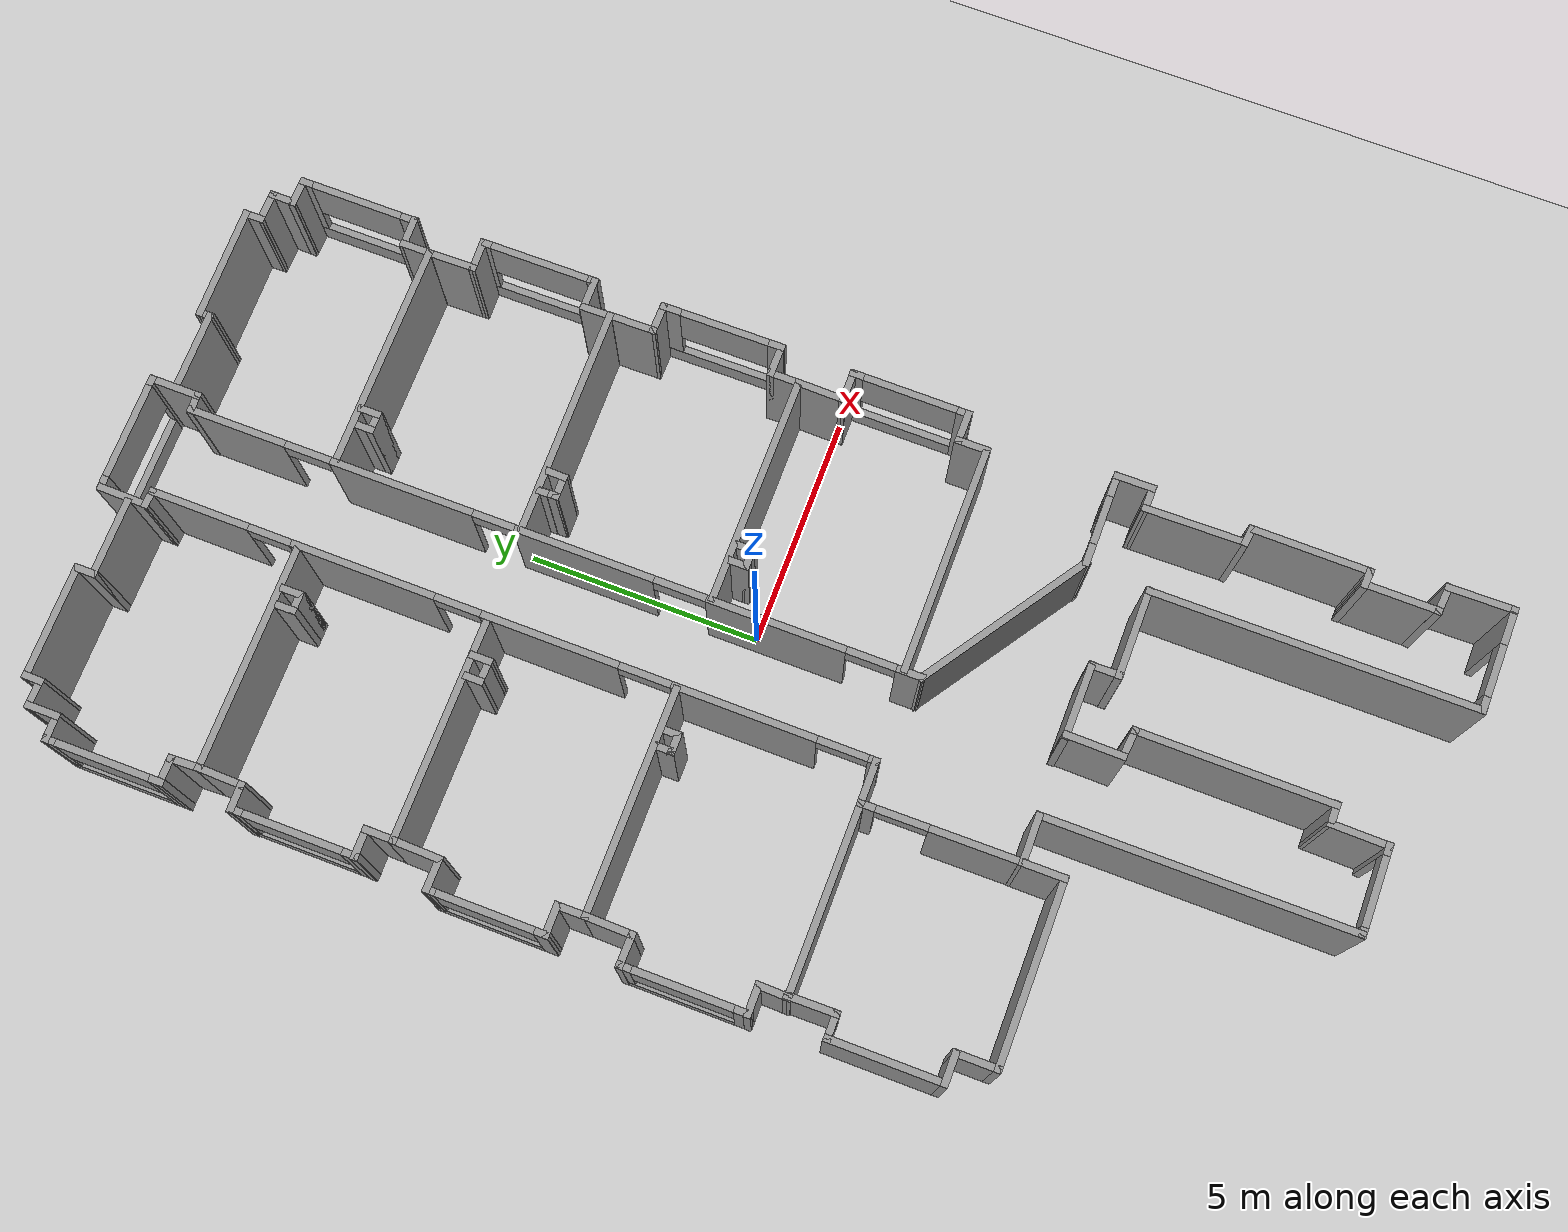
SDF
<sdf version="1.6">
 <world name="default">
  <light name="sun" type="directional">
   <pose>0 0 10 0 -0 0</pose>
   <diffuse>0.8 0.8 0.8 1</diffuse>
   <specular>0.1 0.1 0.1 1</specular>
   <attenuation>
    <range>1000</range>
    <constant>0.9</constant>
    <linear>0.01</linear>
    <quadratic>0.001</quadratic>
   </attenuation>
   <direction>-0.5 0.5 -1</direction>
  </light>
  <model name="ground_plane">
   <static>1</static>
   <link name="link">
    <collision name="collision">
     <geometry><plane><normal>0 0 1</normal><size>100 100</size></plane></geometry>
     <surface><friction><ode><mu>100</mu><mu2>50</mu2></ode></friction></surface>
    </collision>
    <visual name="visual">
     <cast_shadows>0</cast_shadows>
     <geometry><plane><normal>0 0 1</normal><size>100 100</size></plane></geometry>
     <material>
      <script><uri>file://media/materials/scripts/gazebo.material</uri><name>Gazebo/Grey</name></script>
     </material>
    </visual>
   </link>
  </model>
  <gravity>0 0 -9.8</gravity>
  <magnetic_field>6e-06 2.3e-05 -4.2e-05</magnetic_field>
  <atmosphere type="adiabatic"/>
  <physics name="default_physics" default="0" type="ode">
   <max_step_size>0.001</max_step_size>
   <real_time_factor>1</real_time_factor>
   <real_time_update_rate>1000</real_time_update_rate>
  </physics>
  <scene><ambient>0.4 0.4 0.4 1</ambient><background>0.7 0.7 0.7 1</background><shadows>1</shadows></scene>
  <spherical_coordinates>
   <surface_model>EARTH_WGS84</surface_model>
   <latitude_deg>0</latitude_deg>
   <longitude_deg>0</longitude_deg>
   <elevation>0</elevation>
   <heading_deg>0</heading_deg>
  </spherical_coordinates>
  <model name="Ex-diei">
   <pose>-1.07269 -0.427691 0 0 -0 0</pose>
   <link name="Wall_10">
    <collision name="Wall_10_Collision">
     <geometry><box><size>1.32907 0.15 2.5</size></box></geometry>
     <pose>0 0 1.25 0 -0 0</pose>
    </collision>
    <visual name="Wall_10_Visual">
     <pose>0 0 1.25 0 -0 0</pose>
     <geometry><box><size>1.32907 0.15 2.5</size></box></geometry>
     <material>
      <script><uri>file://media/materials/scripts/gazebo.material</uri><name>Gazebo/Grey</name></script>
      <ambient>1 1 1 1</ambient>
     </material>
    </visual>
    <pose>0.944777 -12.0468 0 0 -0 1.55789</pose>
   </link>
   <link name="Wall_100">
    <collision name="Wall_100_Collision">
     <geometry><box><size>0.732631 0.15 2.5</size></box></geometry>
     <pose>0 0 1.25 0 -0 0</pose>
    </collision>
    <visual name="Wall_100_Visual">
     <pose>0 0 1.25 0 -0 0</pose>
     <geometry><box><size>0.732631 0.15 2.5</size></box></geometry>
     <material>
      <script><uri>file://media/materials/scripts/gazebo.material</uri><name>Gazebo/Grey</name></script>
      <ambient>1 1 1 1</ambient>
     </material>
    </visual>
    <pose>5.55171 12.961 0 0 -0 3.12236</pose>
   </link>
   <link name="Wall_101">
    <collision name="Wall_101_Collision">
     <geometry><box><size>0.486208 0.15 2.5</size></box></geometry>
     <pose>0 0 1.25 0 -0 0</pose>
    </collision>
    <visual name="Wall_101_Visual">
     <pose>0 0 1.25 0 -0 0</pose>
     <geometry><box><size>0.486208 0.15 2.5</size></box></geometry>
     <material>
      <script><uri>file://media/materials/scripts/gazebo.material</uri><name>Gazebo/Grey</name></script>
      <ambient>1 1 1 1</ambient>
     </material>
    </visual>
    <pose>5.25829 13.1344 0 0 -0 1.58363</pose>
   </link>
   <link name="Wall_102">
    <collision name="Wall_102_Collision">
     <geometry><box><size>2.49145 0.15 2.5</size></box></geometry>
     <pose>0 0 1.25 0 -0 0</pose>
    </collision>
    <visual name="Wall_102_Visual">
     <pose>0 0 1.25 0 -0 0</pose>
     <geometry><box><size>2.49145 0.15 2.5</size></box></geometry>
     <material>
      <script><uri>file://media/materials/scripts/gazebo.material</uri><name>Gazebo/Grey</name></script>
      <ambient>1 1 1 1</ambient>
     </material>
    </visual>
    <pose>4.08979 13.2913 0 0 0 -3.13236</pose>
   </link>
   <link name="Wall_103">
    <collision name="Wall_103_Collision">
     <geometry><box><size>0.362449 0.15 2.5</size></box></geometry>
     <pose>0 0 1.25 0 -0 0</pose>
    </collision>
    <visual name="Wall_103_Visual">
     <pose>0 0 1.25 0 -0 0</pose>
     <geometry><box><size>0.362449 0.15 2.5</size></box></geometry>
     <material>
      <script><uri>file://media/materials/scripts/gazebo.material</uri><name>Gazebo/Grey</name></script>
      <ambient>1 1 1 1</ambient>
     </material>
    </visual>
    <pose>2.92127 13.1743 0 0 0 -1.55045</pose>
   </link>
   <link name="Wall_104">
    <collision name="Wall_104_Collision">
     <geometry><box><size>1.75 0.15 2.5</size></box></geometry>
     <pose>0 0 1.25 0 -0 0</pose>
    </collision>
    <visual name="Wall_104_Visual">
     <pose>0 0 1.25 0 -0 0</pose>
     <geometry><box><size>1.75 0.15 2.5</size></box></geometry>
     <material>
      <script><uri>file://media/materials/scripts/gazebo.material</uri><name>Gazebo/Grey</name></script>
      <ambient>1 1 1 1</ambient>
     </material>
    </visual>
    <pose>2.11911 13.0681 0 0 -0 3.14159</pose>
   </link>
   <link name="Wall_106">
    <collision name="Wall_106_Collision">
     <geometry><box><size>4.99982 0.15 2.5</size></box></geometry>
     <pose>0 0 1.25 0 -0 0</pose>
    </collision>
    <visual name="Wall_106_Visual">
     <pose>0 0 1.25 0 -0 0</pose>
     <geometry><box><size>4.99982 0.15 2.5</size></box></geometry>
     <material>
      <script><uri>file://media/materials/scripts/gazebo.material</uri><name>Gazebo/Grey</name></script>
      <ambient>1 1 1 1</ambient>
     </material>
    </visual>
    <pose>3.38383 5.40187 0 0 -0 0.00924</pose>
   </link>
   <link name="Wall_107">
    <collision name="Wall_107_Collision">
     <geometry><box><size>0.711686 0.15 2.5</size></box></geometry>
     <pose>0 0 1.25 0 -0 0</pose>
    </collision>
    <visual name="Wall_107_Visual">
     <pose>0 0 1.25 0 -0 0</pose>
     <geometry><box><size>0.711686 0.15 2.5</size></box></geometry>
     <material>
      <script><uri>file://media/materials/scripts/gazebo.material</uri><name>Gazebo/Grey</name></script>
      <ambient>1 1 1 1</ambient>
     </material>
    </visual>
    <pose>5.80561 5.7051 0 0 -0 1.58155</pose>
   </link>
   <link name="Wall_108">
    <collision name="Wall_108_Collision">
     <geometry><box><size>0.750065 0.15 2.5</size></box></geometry>
     <pose>0 0 1.25 0 -0 0</pose>
    </collision>
    <visual name="Wall_108_Visual">
     <pose>0 0 1.25 0 -0 0</pose>
     <geometry><box><size>0.750065 0.15 2.5</size></box></geometry>
     <material>
      <script><uri>file://media/materials/scripts/gazebo.material</uri><name>Gazebo/Grey</name></script>
      <ambient>1 1 1 1</ambient>
     </material>
    </visual>
    <pose>6.10261 5.99563 0 0 -0 0.010773</pose>
   </link>
   <link name="Wall_109">
    <pose>6.40339 7.22457 0 0 -0 1.57542</pose>
    <visual name="Wall_109_Visual_0">
     <pose>-1.19042 0 1.25 0 -0 0</pose>
     <geometry><box><size>0.233536 0.15 2.5</size></box></geometry>
     <material>
      <script><uri>file://media/materials/scripts/gazebo.material</uri><name>Gazebo/Grey</name></script>
      <ambient>1 1 1 1</ambient>
     </material>
    </visual>
    <collision name="Wall_109_Collision_0">
     <geometry><box><size>0.233536 0.15 2.5</size></box></geometry>
     <pose>-1.19042 0 1.25 0 -0 0</pose>
    </collision>
    <visual name="Wall_109_Visual_1">
     <pose>0.116768 0 0.25 0 -0 0</pose>
     <geometry><box><size>2.38084 0.15 0.5</size></box></geometry>
     <material>
      <script><uri>file://media/materials/scripts/gazebo.material</uri><name>Gazebo/Grey</name></script>
      <ambient>1 1 1 1</ambient>
     </material>
    </visual>
    <collision name="Wall_109_Collision_1">
     <geometry><box><size>2.38084 0.15 0.5</size></box></geometry>
     <pose>0.116768 0 0.25 0 -0 0</pose>
    </collision>
    <visual name="Wall_109_Visual_2">
     <pose>1.1833 0 1.5 0 -0 0</pose>
     <geometry><box><size>0.247773 0.15 2</size></box></geometry>
     <material>
      <script><uri>file://media/materials/scripts/gazebo.material</uri><name>Gazebo/Grey</name></script>
      <ambient>1 1 1 1</ambient>
     </material>
    </visual>
    <collision name="Wall_109_Collision_2">
     <geometry><box><size>0.247773 0.15 2</size></box></geometry>
     <pose>1.1833 0 1.5 0 -0 0</pose>
    </collision>
    <visual name="Wall_109_Visual_3">
     <pose>-0.007119 0 1.9 0 -0 0</pose>
     <geometry><box><size>2.13307 0.15 1.2</size></box></geometry>
     <material>
      <script><uri>file://media/materials/scripts/gazebo.material</uri><name>Gazebo/Grey</name></script>
      <ambient>1 1 1 1</ambient>
     </material>
    </visual>
    <collision name="Wall_109_Collision_3">
     <geometry><box><size>2.13307 0.15 1.2</size></box></geometry>
     <pose>-0.007119 0 1.9 0 -0 0</pose>
    </collision>
   </link>
   <link name="Wall_11">
    <collision name="Wall_11_Collision">
     <geometry><box><size>0.5516 0.15 2.5</size></box></geometry>
     <pose>0 0 1.25 0 -0 0</pose>
    </collision>
    <visual name="Wall_11_Visual">
     <pose>0 0 1.25 0 -0 0</pose>
     <geometry><box><size>0.5516 0.15 2.5</size></box></geometry>
     <material>
      <script><uri>file://media/materials/scripts/gazebo.material</uri><name>Gazebo/Grey</name></script>
      <ambient>1 1 1 1</ambient>
     </material>
    </visual>
    <pose>1.15318 -11.4585 0 0 0 -0.004913</pose>
   </link>
   <link name="Wall_110">
    <collision name="Wall_110_Collision">
     <geometry><box><size>0.737495 0.15 2.5</size></box></geometry>
     <pose>0 0 1.25 0 -0 0</pose>
    </collision>
    <visual name="Wall_110_Visual">
     <pose>0 0 1.25 0 -0 0</pose>
     <geometry><box><size>0.737495 0.15 2.5</size></box></geometry>
     <material>
      <script><uri>file://media/materials/scripts/gazebo.material</uri><name>Gazebo/Grey</name></script>
      <ambient>1 1 1 1</ambient>
     </material>
    </visual>
    <pose>6.09764 8.45351 0 0 0 -3.10858</pose>
   </link>
   <link name="Wall_111">
    <collision name="Wall_111_Collision">
     <geometry><box><size>1.11417 0.15 2.5</size></box></geometry>
     <pose>0 0 1.25 0 -0 0</pose>
    </collision>
    <visual name="Wall_111_Visual">
     <pose>0 0 1.25 0 -0 0</pose>
     <geometry><box><size>1.11417 0.15 2.5</size></box></geometry>
     <material>
      <script><uri>file://media/materials/scripts/gazebo.material</uri><name>Gazebo/Grey</name></script>
      <ambient>1 1 1 1</ambient>
     </material>
    </visual>
    <pose>5.79813 8.93083 0 0 -0 1.58308</pose>
   </link>
   <link name="Wall_115">
    <collision name="Wall_115_Collision">
     <geometry><box><size>0.5 0.15 2.5</size></box></geometry>
     <pose>0 0 1.25 0 -0 0</pose>
    </collision>
    <visual name="Wall_115_Visual">
     <pose>0 0 1.25 0 -0 0</pose>
     <geometry><box><size>0.5 0.15 2.5</size></box></geometry>
     <material>
      <script><uri>file://media/materials/scripts/gazebo.material</uri><name>Gazebo/Grey</name></script>
      <ambient>1 1 1 1</ambient>
     </material>
    </visual>
    <pose>1.81628 9.19179 0 0 0 -1.5708</pose>
   </link>
   <link name="Wall_116">
    <collision name="Wall_116_Collision">
     <geometry><box><size>0.5 0.15 2.5</size></box></geometry>
     <pose>0 0 1.25 0 -0 0</pose>
    </collision>
    <visual name="Wall_116_Visual">
     <pose>0 0 1.25 0 -0 0</pose>
     <geometry><box><size>0.5 0.15 2.5</size></box></geometry>
     <material>
      <script><uri>file://media/materials/scripts/gazebo.material</uri><name>Gazebo/Grey</name></script>
      <ambient>1 1 1 1</ambient>
     </material>
    </visual>
    <pose>1.99127 9.01679 0 0 -0 0</pose>
   </link>
   <link name="Wall_117">
    <collision name="Wall_117_Collision">
     <geometry><box><size>0.5 0.15 2.5</size></box></geometry>
     <pose>0 0 1.25 0 -0 0</pose>
    </collision>
    <visual name="Wall_117_Visual">
     <pose>0 0 1.25 0 -0 0</pose>
     <geometry><box><size>0.5 0.15 2.5</size></box></geometry>
     <material>
      <script><uri>file://media/materials/scripts/gazebo.material</uri><name>Gazebo/Grey</name></script>
      <ambient>1 1 1 1</ambient>
     </material>
    </visual>
    <pose>2.16628 9.19179 0 0 -0 1.5708</pose>
   </link>
   <link name="Wall_119">
    <collision name="Wall_119_Collision">
     <geometry><box><size>5 0.15 2.5</size></box></geometry>
     <pose>0 0 1.25 0 -0 0</pose>
    </collision>
    <visual name="Wall_119_Visual">
     <pose>0 0 1.25 0 -0 0</pose>
     <geometry><box><size>5 0.15 2.5</size></box></geometry>
     <material>
      <script><uri>file://media/materials/scripts/gazebo.material</uri><name>Gazebo/Grey</name></script>
      <ambient>1 1 1 1</ambient>
     </material>
    </visual>
    <pose>3.38195 1.30322 0 0 -0 0</pose>
   </link>
   <link name="Wall_12">
    <collision name="Wall_12_Collision">
     <geometry><box><size>4.25837 0.15 2.5</size></box></geometry>
     <pose>0 0 1.25 0 -0 0</pose>
    </collision>
    <visual name="Wall_12_Visual">
     <pose>0 0 1.25 0 -0 0</pose>
     <geometry><box><size>4.25837 0.15 2.5</size></box></geometry>
     <material>
      <script><uri>file://media/materials/scripts/gazebo.material</uri><name>Gazebo/Grey</name></script>
      <ambient>1 1 1 1</ambient>
     </material>
    </visual>
    <pose>1.35469 -9.4053 0 0 -0 1.56675</pose>
   </link>
   <link name="Wall_120">
    <collision name="Wall_120_Collision">
     <geometry><box><size>0.75 0.15 2.5</size></box></geometry>
     <pose>0 0 1.25 0 -0 0</pose>
    </collision>
    <visual name="Wall_120_Visual">
     <pose>0 0 1.25 0 -0 0</pose>
     <geometry><box><size>0.75 0.15 2.5</size></box></geometry>
     <material>
      <script><uri>file://media/materials/scripts/gazebo.material</uri><name>Gazebo/Grey</name></script>
      <ambient>1 1 1 1</ambient>
     </material>
    </visual>
    <pose>5.80695 1.60322 0 0 -0 1.5708</pose>
   </link>
   <link name="Wall_121">
    <collision name="Wall_121_Collision">
     <geometry><box><size>0.75 0.15 2.5</size></box></geometry>
     <pose>0 0 1.25 0 -0 0</pose>
    </collision>
    <visual name="Wall_121_Visual">
     <pose>0 0 1.25 0 -0 0</pose>
     <geometry><box><size>0.75 0.15 2.5</size></box></geometry>
     <material>
      <script><uri>file://media/materials/scripts/gazebo.material</uri><name>Gazebo/Grey</name></script>
      <ambient>1 1 1 1</ambient>
     </material>
    </visual>
    <pose>6.10695 1.90322 0 0 -0 0</pose>
   </link>
   <link name="Wall_122">
    <pose>6.39956 3.18474 0 0 -0 1.57656</pose>
    <visual name="Wall_122_Visual_0">
     <pose>-1.18243 0 1.25 0 -0 0</pose>
     <geometry><box><size>0.348224 0.15 2.5</size></box></geometry>
     <material>
      <script><uri>file://media/materials/scripts/gazebo.material</uri><name>Gazebo/Grey</name></script>
      <ambient>1 1 1 1</ambient>
     </material>
    </visual>
    <collision name="Wall_122_Collision_0">
     <geometry><box><size>0.348224 0.15 2.5</size></box></geometry>
     <pose>-1.18243 0 1.25 0 -0 0</pose>
    </collision>
    <visual name="Wall_122_Visual_1">
     <pose>0.174112 0 0.25 0 -0 0</pose>
     <geometry><box><size>2.36486 0.15 0.5</size></box></geometry>
     <material>
      <script><uri>file://media/materials/scripts/gazebo.material</uri><name>Gazebo/Grey</name></script>
      <ambient>1 1 1 1</ambient>
     </material>
    </visual>
    <collision name="Wall_122_Collision_1">
     <geometry><box><size>2.36486 0.15 0.5</size></box></geometry>
     <pose>0.174112 0 0.25 0 -0 0</pose>
    </collision>
    <visual name="Wall_122_Visual_2">
     <pose>1.12978 0 1.5 0 -0 0</pose>
     <geometry><box><size>0.453513 0.15 2</size></box></geometry>
     <material>
      <script><uri>file://media/materials/scripts/gazebo.material</uri><name>Gazebo/Grey</name></script>
      <ambient>1 1 1 1</ambient>
     </material>
    </visual>
    <collision name="Wall_122_Collision_2">
     <geometry><box><size>0.453513 0.15 2</size></box></geometry>
     <pose>1.12978 0 1.5 0 -0 0</pose>
    </collision>
    <visual name="Wall_122_Visual_3">
     <pose>-0.052644 0 1.9 0 -0 0</pose>
     <geometry><box><size>1.91135 0.15 1.2</size></box></geometry>
     <material>
      <script><uri>file://media/materials/scripts/gazebo.material</uri><name>Gazebo/Grey</name></script>
      <ambient>1 1 1 1</ambient>
     </material>
    </visual>
    <collision name="Wall_122_Collision_3">
     <geometry><box><size>1.91135 0.15 1.2</size></box></geometry>
     <pose>-0.052644 0 1.9 0 -0 0</pose>
    </collision>
   </link>
   <link name="Wall_123">
    <collision name="Wall_123_Collision">
     <geometry><box><size>0.716608 0.15 2.5</size></box></geometry>
     <pose>0 0 1.25 0 -0 0</pose>
    </collision>
    <visual name="Wall_123_Visual">
     <pose>0 0 1.25 0 -0 0</pose>
     <geometry><box><size>0.716608 0.15 2.5</size></box></geometry>
     <material>
      <script><uri>file://media/materials/scripts/gazebo.material</uri><name>Gazebo/Grey</name></script>
      <ambient>1 1 1 1</ambient>
     </material>
    </visual>
    <pose>6.10886 4.47426 0 0 -0 3.12641</pose>
   </link>
   <link name="Wall_124">
    <collision name="Wall_124_Collision">
     <geometry><box><size>1.0872 0.15 2.5</size></box></geometry>
     <pose>0 0 1.25 0 -0 0</pose>
    </collision>
    <visual name="Wall_124_Visual">
     <pose>0 0 1.25 0 -0 0</pose>
     <geometry><box><size>1.0872 0.15 2.5</size></box></geometry>
     <material>
      <script><uri>file://media/materials/scripts/gazebo.material</uri><name>Gazebo/Grey</name></script>
      <ambient>1 1 1 1</ambient>
     </material>
    </visual>
    <pose>5.82137 4.94714 0 0 -0 1.57973</pose>
   </link>
   <link name="Wall_126">
    <collision name="Wall_126_Collision">
     <geometry><box><size>0.25 0.15 2.5</size></box></geometry>
     <pose>0 0 1.25 0 -0 0</pose>
    </collision>
    <visual name="Wall_126_Visual">
     <pose>0 0 1.25 0 -0 0</pose>
     <geometry><box><size>0.25 0.15 2.5</size></box></geometry>
     <material>
      <script><uri>file://media/materials/scripts/gazebo.material</uri><name>Gazebo/Grey</name></script>
      <ambient>1 1 1 1</ambient>
     </material>
    </visual>
    <pose>1.81991 5.27998 0 0 0 -1.5708</pose>
   </link>
   <link name="Wall_128">
    <collision name="Wall_128_Collision">
     <geometry><box><size>0.493722 0.15 2.5</size></box></geometry>
     <pose>0 0 1.25 0 -0 0</pose>
    </collision>
    <visual name="Wall_128_Visual">
     <pose>0 0 1.25 0 -0 0</pose>
     <geometry><box><size>0.493722 0.15 2.5</size></box></geometry>
     <material>
      <script><uri>file://media/materials/scripts/gazebo.material</uri><name>Gazebo/Grey</name></script>
      <ambient>1 1 1 1</ambient>
     </material>
    </visual>
    <pose>2.26046 5.16946 0 0 0 -1.60137</pose>
   </link>
   <link name="Wall_129">
    <collision name="Wall_129_Collision">
     <geometry><box><size>0.575524 0.15 2.5</size></box></geometry>
     <pose>0 0 1.25 0 -0 0</pose>
    </collision>
    <visual name="Wall_129_Visual">
     <pose>0 0 1.25 0 -0 0</pose>
     <geometry><box><size>0.575524 0.15 2.5</size></box></geometry>
     <material>
      <script><uri>file://media/materials/scripts/gazebo.material</uri><name>Gazebo/Grey</name></script>
      <ambient>1 1 1 1</ambient>
     </material>
    </visual>
    <pose>2.04245 4.99558 0 0 0 -3.13172</pose>
   </link>
   <link name="Wall_13">
    <collision name="Wall_13_Collision">
     <geometry><box><size>0.707666 0.15 2.5</size></box></geometry>
     <pose>0 0 1.25 0 -0 0</pose>
    </collision>
    <visual name="Wall_13_Visual">
     <pose>0 0 1.25 0 -0 0</pose>
     <geometry><box><size>0.707666 0.15 2.5</size></box></geometry>
     <material>
      <script><uri>file://media/materials/scripts/gazebo.material</uri><name>Gazebo/Grey</name></script>
      <ambient>1 1 1 1</ambient>
     </material>
    </visual>
    <pose>1.08546 -7.32452 0 0 -0 3.046</pose>
   </link>
   <link name="Wall_130">
    <collision name="Wall_130_Collision">
     <geometry><box><size>0.467311 0.15 2.5</size></box></geometry>
     <pose>0 0 1.25 0 -0 0</pose>
    </collision>
    <visual name="Wall_130_Visual">
     <pose>0 0 1.25 0 -0 0</pose>
     <geometry><box><size>0.467311 0.15 2.5</size></box></geometry>
     <material>
      <script><uri>file://media/materials/scripts/gazebo.material</uri><name>Gazebo/Grey</name></script>
      <ambient>1 1 1 1</ambient>
     </material>
    </visual>
    <pose>1.82812 5.15213 0 0 -0 1.58073</pose>
   </link>
   <link name="Wall_132">
    <collision name="Wall_132_Collision">
     <geometry><box><size>5 0.15 2.5</size></box></geometry>
     <pose>0 0 1.25 0 -0 0</pose>
    </collision>
    <visual name="Wall_132_Visual">
     <pose>0 0 1.25 0 -0 0</pose>
     <geometry><box><size>5 0.15 2.5</size></box></geometry>
     <material>
      <script><uri>file://media/materials/scripts/gazebo.material</uri><name>Gazebo/Grey</name></script>
      <ambient>1 1 1 1</ambient>
     </material>
    </visual>
    <pose>3.36331 -2.7403 0 0 -0 0</pose>
   </link>
   <link name="Wall_133">
    <collision name="Wall_133_Collision">
     <geometry><box><size>0.75 0.15 2.5</size></box></geometry>
     <pose>0 0 1.25 0 -0 0</pose>
    </collision>
    <visual name="Wall_133_Visual">
     <pose>0 0 1.25 0 -0 0</pose>
     <geometry><box><size>0.75 0.15 2.5</size></box></geometry>
     <material>
      <script><uri>file://media/materials/scripts/gazebo.material</uri><name>Gazebo/Grey</name></script>
      <ambient>1 1 1 1</ambient>
     </material>
    </visual>
    <pose>5.78831 -2.4403 0 0 -0 1.5708</pose>
   </link>
   <link name="Wall_134">
    <collision name="Wall_134_Collision">
     <geometry><box><size>0.75 0.15 2.5</size></box></geometry>
     <pose>0 0 1.25 0 -0 0</pose>
    </collision>
    <visual name="Wall_134_Visual">
     <pose>0 0 1.25 0 -0 0</pose>
     <geometry><box><size>0.75 0.15 2.5</size></box></geometry>
     <material>
      <script><uri>file://media/materials/scripts/gazebo.material</uri><name>Gazebo/Grey</name></script>
      <ambient>1 1 1 1</ambient>
     </material>
    </visual>
    <pose>6.08831 -2.1403 0 0 -0 0</pose>
   </link>
   <link name="Wall_135">
    <pose>6.39016 -0.900619 0 0 -0 1.56931</pose>
    <visual name="Wall_135_Visual_0">
     <pose>-1.15835 0 1.25 0 -0 0</pose>
     <geometry><box><size>0.312668 0.15 2.5</size></box></geometry>
     <material>
      <script><uri>file://media/materials/scripts/gazebo.material</uri><name>Gazebo/Grey</name></script>
      <ambient>1 1 1 1</ambient>
     </material>
    </visual>
    <collision name="Wall_135_Collision_0">
     <geometry><box><size>0.312668 0.15 2.5</size></box></geometry>
     <pose>-1.15835 0 1.25 0 -0 0</pose>
    </collision>
    <visual name="Wall_135_Visual_1">
     <pose>0.156334 0 0.25 0 -0 0</pose>
     <geometry><box><size>2.3167 0.15 0.5</size></box></geometry>
     <material>
      <script><uri>file://media/materials/scripts/gazebo.material</uri><name>Gazebo/Grey</name></script>
      <ambient>1 1 1 1</ambient>
     </material>
    </visual>
    <collision name="Wall_135_Collision_1">
     <geometry><box><size>2.3167 0.15 0.5</size></box></geometry>
     <pose>0.156334 0 0.25 0 -0 0</pose>
    </collision>
    <visual name="Wall_135_Visual_2">
     <pose>1.16086 0 1.5 0 -0 0</pose>
     <geometry><box><size>0.30765 0.15 2</size></box></geometry>
     <material>
      <script><uri>file://media/materials/scripts/gazebo.material</uri><name>Gazebo/Grey</name></script>
      <ambient>1 1 1 1</ambient>
     </material>
    </visual>
    <collision name="Wall_135_Collision_2">
     <geometry><box><size>0.30765 0.15 2</size></box></geometry>
     <pose>1.16086 0 1.5 0 -0 0</pose>
    </collision>
    <visual name="Wall_135_Visual_3">
     <pose>0.002509 0 1.9 0 -0 0</pose>
     <geometry><box><size>2.00905 0.15 1.2</size></box></geometry>
     <material>
      <script><uri>file://media/materials/scripts/gazebo.material</uri><name>Gazebo/Grey</name></script>
      <ambient>1 1 1 1</ambient>
     </material>
    </visual>
    <collision name="Wall_135_Collision_3">
     <geometry><box><size>2.00905 0.15 1.2</size></box></geometry>
     <pose>0.002509 0 1.9 0 -0 0</pose>
    </collision>
   </link>
   <link name="Wall_136">
    <collision name="Wall_136_Collision">
     <geometry><box><size>0.75 0.15 2.5</size></box></geometry>
     <pose>0 0 1.25 0 -0 0</pose>
    </collision>
    <visual name="Wall_136_Visual">
     <pose>0 0 1.25 0 -0 0</pose>
     <geometry><box><size>0.75 0.15 2.5</size></box></geometry>
     <material>
      <script><uri>file://media/materials/scripts/gazebo.material</uri><name>Gazebo/Grey</name></script>
      <ambient>1 1 1 1</ambient>
     </material>
    </visual>
    <pose>6.09201 0.335366 0 0 -0 3.14159</pose>
   </link>
   <link name="Wall_137">
    <collision name="Wall_137_Collision">
     <geometry><box><size>1.11427 0.15 2.5</size></box></geometry>
     <pose>0 0 1.25 0 -0 0</pose>
    </collision>
    <visual name="Wall_137_Visual">
     <pose>0 0 1.25 0 -0 0</pose>
     <geometry><box><size>1.11427 0.15 2.5</size></box></geometry>
     <material>
      <script><uri>file://media/materials/scripts/gazebo.material</uri><name>Gazebo/Grey</name></script>
      <ambient>1 1 1 1</ambient>
     </material>
    </visual>
    <pose>5.79948 0.821141 0 0 -0 1.5553</pose>
   </link>
   <link name="Wall_139">
    <collision name="Wall_139_Collision">
     <geometry><box><size>0.5 0.15 2.5</size></box></geometry>
     <pose>0 0 1.25 0 -0 0</pose>
    </collision>
    <visual name="Wall_139_Visual">
     <pose>0 0 1.25 0 -0 0</pose>
     <geometry><box><size>0.5 0.15 2.5</size></box></geometry>
     <material>
      <script><uri>file://media/materials/scripts/gazebo.material</uri><name>Gazebo/Grey</name></script>
      <ambient>1 1 1 1</ambient>
     </material>
    </visual>
    <pose>1.81114 1.09434 0 0 0 -1.5708</pose>
   </link>
   <link name="Wall_14">
    <collision name="Wall_14_Collision">
     <geometry><box><size>1.32107 0.15 2.5</size></box></geometry>
     <pose>0 0 1.25 0 -0 0</pose>
    </collision>
    <visual name="Wall_14_Visual">
     <pose>0 0 1.25 0 -0 0</pose>
     <geometry><box><size>1.32107 0.15 2.5</size></box></geometry>
     <material>
      <script><uri>file://media/materials/scripts/gazebo.material</uri><name>Gazebo/Grey</name></script>
      <ambient>1 1 1 1</ambient>
     </material>
    </visual>
    <pose>0.807898 -6.71237 0 0 -0 1.55781</pose>
   </link>
   <link name="Wall_140">
    <collision name="Wall_140_Collision">
     <geometry><box><size>0.5 0.15 2.5</size></box></geometry>
     <pose>0 0 1.25 0 -0 0</pose>
    </collision>
    <visual name="Wall_140_Visual">
     <pose>0 0 1.25 0 -0 0</pose>
     <geometry><box><size>0.5 0.15 2.5</size></box></geometry>
     <material>
      <script><uri>file://media/materials/scripts/gazebo.material</uri><name>Gazebo/Grey</name></script>
      <ambient>1 1 1 1</ambient>
     </material>
    </visual>
    <pose>1.98614 0.919343 0 0 -0 0</pose>
   </link>
   <link name="Wall_141">
    <collision name="Wall_141_Collision">
     <geometry><box><size>0.5 0.15 2.5</size></box></geometry>
     <pose>0 0 1.25 0 -0 0</pose>
    </collision>
    <visual name="Wall_141_Visual">
     <pose>0 0 1.25 0 -0 0</pose>
     <geometry><box><size>0.5 0.15 2.5</size></box></geometry>
     <material>
      <script><uri>file://media/materials/scripts/gazebo.material</uri><name>Gazebo/Grey</name></script>
      <ambient>1 1 1 1</ambient>
     </material>
    </visual>
    <pose>2.16114 1.09434 0 0 -0 1.5708</pose>
   </link>
   <link name="Wall_15">
    <collision name="Wall_15_Collision">
     <geometry><box><size>1.67095 0.15 2.5</size></box></geometry>
     <pose>0 0 1.25 0 -0 0</pose>
    </collision>
    <visual name="Wall_15_Visual">
     <pose>0 0 1.25 0 -0 0</pose>
     <geometry><box><size>1.67095 0.15 2.5</size></box></geometry>
     <material>
      <script><uri>file://media/materials/scripts/gazebo.material</uri><name>Gazebo/Grey</name></script>
      <ambient>1 1 1 1</ambient>
     </material>
    </visual>
    <pose>1.55313 -6.13444 0 0 0 -0.01</pose>
   </link>
   <link name="Wall_16">
    <collision name="Wall_16_Collision">
     <geometry><box><size>0.726398 0.15 2.5</size></box></geometry>
     <pose>0 0 1.25 0 -0 0</pose>
    </collision>
    <visual name="Wall_16_Visual">
     <pose>0 0 1.25 0 -0 0</pose>
     <geometry><box><size>0.726398 0.15 2.5</size></box></geometry>
     <material>
      <script><uri>file://media/materials/scripts/gazebo.material</uri><name>Gazebo/Grey</name></script>
      <ambient>1 1 1 1</ambient>
     </material>
    </visual>
    <pose>2.30936 -6.43021 0 0 0 -1.55899</pose>
   </link>
   <link name="Wall_17">
    <collision name="Wall_17_Collision">
     <geometry><box><size>2.00096 0.15 2.5</size></box></geometry>
     <pose>0 0 1.25 0 -0 0</pose>
    </collision>
    <visual name="Wall_17_Visual">
     <pose>0 0 1.25 0 -0 0</pose>
     <geometry><box><size>2.00096 0.15 2.5</size></box></geometry>
     <material>
      <script><uri>file://media/materials/scripts/gazebo.material</uri><name>Gazebo/Grey</name></script>
      <ambient>1 1 1 1</ambient>
     </material>
    </visual>
    <pose>3.23063 -6.71457 0 0 0 -0.004108</pose>
   </link>
   <link name="Wall_18">
    <collision name="Wall_18_Collision">
     <geometry><box><size>7 0.15 2.5</size></box></geometry>
     <pose>0 0 1.25 0 -0 0</pose>
    </collision>
    <visual name="Wall_18_Visual">
     <pose>0 0 1.25 0 -0 0</pose>
     <geometry><box><size>7 0.15 2.5</size></box></geometry>
     <material>
      <script><uri>file://media/materials/scripts/gazebo.material</uri><name>Gazebo/Grey</name></script>
      <ambient>1 1 1 1</ambient>
     </material>
    </visual>
    <pose>4.1485 -10.151 0 0 0 -1.5708</pose>
   </link>
   <link name="Wall_19">
    <pose>5.23985 -13.5798 0 0 0 -0.010525</pose>
    <visual name="Wall_19_Visual_0">
     <pose>-0.977654 0 1.25 0 -0 0</pose>
     <geometry><box><size>0.362307 0.15 2.5</size></box></geometry>
     <material>
      <script><uri>file://media/materials/scripts/gazebo.material</uri><name>Gazebo/Grey</name></script>
      <ambient>1 1 1 1</ambient>
     </material>
    </visual>
    <collision name="Wall_19_Collision_0">
     <geometry><box><size>0.362307 0.15 2.5</size></box></geometry>
     <pose>-0.977654 0 1.25 0 -0 0</pose>
    </collision>
    <visual name="Wall_19_Visual_1">
     <pose>0.744469 0 1.25 0 -0 0</pose>
     <geometry><box><size>0.828677 0.15 2.5</size></box></geometry>
     <material>
      <script><uri>file://media/materials/scripts/gazebo.material</uri><name>Gazebo/Grey</name></script>
      <ambient>1 1 1 1</ambient>
     </material>
    </visual>
    <collision name="Wall_19_Collision_1">
     <geometry><box><size>0.828677 0.15 2.5</size></box></geometry>
     <pose>0.744469 0 1.25 0 -0 0</pose>
    </collision>
    <visual name="Wall_19_Visual_2">
     <pose>-0.233185 0 2.25 0 -0 0</pose>
     <geometry><box><size>1.12663 0.15 0.5</size></box></geometry>
     <material>
      <script><uri>file://media/materials/scripts/gazebo.material</uri><name>Gazebo/Grey</name></script>
      <ambient>1 1 1 1</ambient>
     </material>
    </visual>
    <collision name="Wall_19_Collision_2">
     <geometry><box><size>1.12663 0.15 0.5</size></box></geometry>
     <pose>-0.233185 0 2.25 0 -0 0</pose>
    </collision>
   </link>
   <link name="Wall_2">
    <collision name="Wall_2_Collision">
     <geometry><box><size>1.13505 0.15 2.5</size></box></geometry>
     <pose>0 0 1.25 0 -0 0</pose>
    </collision>
    <visual name="Wall_2_Visual">
     <pose>0 0 1.25 0 -0 0</pose>
     <geometry><box><size>1.13505 0.15 2.5</size></box></geometry>
     <material>
      <script><uri>file://media/materials/scripts/gazebo.material</uri><name>Gazebo/Grey</name></script>
      <ambient>1 1 1 1</ambient>
     </material>
    </visual>
    <pose>-1.22223 13.0876 0 0 0 -1.58602</pose>
   </link>
   <link name="Wall_20">
    <collision name="Wall_20_Collision">
     <geometry><box><size>1.5 0.15 2.5</size></box></geometry>
     <pose>0 0 1.25 0 -0 0</pose>
    </collision>
    <visual name="Wall_20_Visual">
     <pose>0 0 1.25 0 -0 0</pose>
     <geometry><box><size>1.5 0.15 2.5</size></box></geometry>
     <material>
      <script><uri>file://media/materials/scripts/gazebo.material</uri><name>Gazebo/Grey</name></script>
      <ambient>1 1 1 1</ambient>
     </material>
    </visual>
    <pose>6.31599 -12.9162 0 0 -0 1.58206</pose>
   </link>
   <link name="Wall_21">
    <collision name="Wall_21_Collision">
     <geometry><box><size>0.694391 0.15 2.5</size></box></geometry>
     <pose>0 0 1.25 0 -0 0</pose>
    </collision>
    <visual name="Wall_21_Visual">
     <pose>0 0 1.25 0 -0 0</pose>
     <geometry><box><size>0.694391 0.15 2.5</size></box></geometry>
     <material>
      <script><uri>file://media/materials/scripts/gazebo.material</uri><name>Gazebo/Grey</name></script>
      <ambient>1 1 1 1</ambient>
     </material>
    </visual>
    <pose>6.04477 -12.2182 0 0 -0 3.05687</pose>
   </link>
   <link name="Wall_22">
    <collision name="Wall_22_Collision">
     <geometry><box><size>1.67064 0.15 2.5</size></box></geometry>
     <pose>0 0 1.25 0 -0 0</pose>
    </collision>
    <visual name="Wall_22_Visual">
     <pose>0 0 1.25 0 -0 0</pose>
     <geometry><box><size>1.67064 0.15 2.5</size></box></geometry>
     <material>
      <script><uri>file://media/materials/scripts/gazebo.material</uri><name>Gazebo/Grey</name></script>
      <ambient>1 1 1 1</ambient>
     </material>
    </visual>
    <pose>5.78435 -11.4348 0 0 -0 1.5666</pose>
   </link>
   <link name="Wall_23">
    <collision name="Wall_23_Collision">
     <geometry><box><size>0.447159 0.15 2.5</size></box></geometry>
     <pose>0 0 1.25 0 -0 0</pose>
    </collision>
    <visual name="Wall_23_Visual">
     <pose>0 0 1.25 0 -0 0</pose>
     <geometry><box><size>0.447159 0.15 2.5</size></box></geometry>
     <material>
      <script><uri>file://media/materials/scripts/gazebo.material</uri><name>Gazebo/Grey</name></script>
      <ambient>1 1 1 1</ambient>
     </material>
    </visual>
    <pose>5.92832 -10.6821 0 0 0 -0.051203</pose>
   </link>
   <link name="Wall_24">
    <collision name="Wall_24_Collision">
     <geometry><box><size>2.61047 0.15 2.5</size></box></geometry>
     <pose>0 0 1.25 0 -0 0</pose>
    </collision>
    <visual name="Wall_24_Visual">
     <pose>0 0 1.25 0 -0 0</pose>
     <geometry><box><size>2.61047 0.15 2.5</size></box></geometry>
     <material>
      <script><uri>file://media/materials/scripts/gazebo.material</uri><name>Gazebo/Grey</name></script>
      <ambient>1 1 1 1</ambient>
     </material>
    </visual>
    <pose>6.08397 -9.45949 0 0 -0 1.56489</pose>
   </link>
   <link name="Wall_25">
    <collision name="Wall_25_Collision">
     <geometry><box><size>0.465275 0.15 2.5</size></box></geometry>
     <pose>0 0 1.25 0 -0 0</pose>
    </collision>
    <visual name="Wall_25_Visual">
     <pose>0 0 1.25 0 -0 0</pose>
     <geometry><box><size>0.465275 0.15 2.5</size></box></geometry>
     <material>
      <script><uri>file://media/materials/scripts/gazebo.material</uri><name>Gazebo/Grey</name></script>
      <ambient>1 1 1 1</ambient>
     </material>
    </visual>
    <pose>5.92821 -8.21622 0 0 -0 3.01648</pose>
   </link>
   <link name="Wall_26">
    <collision name="Wall_26_Collision">
     <geometry><box><size>2.23033 0.15 2.5</size></box></geometry>
     <pose>0 0 1.25 0 -0 0</pose>
    </collision>
    <visual name="Wall_26_Visual">
     <pose>0 0 1.25 0 -0 0</pose>
     <geometry><box><size>2.23033 0.15 2.5</size></box></geometry>
     <material>
      <script><uri>file://media/materials/scripts/gazebo.material</uri><name>Gazebo/Grey</name></script>
      <ambient>1 1 1 1</ambient>
     </material>
    </visual>
    <pose>5.76519 -7.14985 0 0 -0 1.58351</pose>
   </link>
   <link name="Wall_27">
    <collision name="Wall_27_Collision">
     <geometry><box><size>0.603301 0.15 2.5</size></box></geometry>
     <pose>0 0 1.25 0 -0 0</pose>
    </collision>
    <visual name="Wall_27_Visual">
     <pose>0 0 1.25 0 -0 0</pose>
     <geometry><box><size>0.603301 0.15 2.5</size></box></geometry>
     <material>
      <script><uri>file://media/materials/scripts/gazebo.material</uri><name>Gazebo/Grey</name></script>
      <ambient>1 1 1 1</ambient>
     </material>
    </visual>
    <pose>5.97861 -6.1116 0 0 0 -0.008064</pose>
   </link>
   <link name="Wall_28">
    <collision name="Wall_28_Collision">
     <geometry><box><size>0.887652 0.15 2.5</size></box></geometry>
     <pose>0 0 1.25 0 -0 0</pose>
    </collision>
    <visual name="Wall_28_Visual">
     <pose>0 0 1.25 0 -0 0</pose>
     <geometry><box><size>0.887652 0.15 2.5</size></box></geometry>
     <material>
      <script><uri>file://media/materials/scripts/gazebo.material</uri><name>Gazebo/Grey</name></script>
      <ambient>1 1 1 1</ambient>
     </material>
    </visual>
    <pose>6.20344 -5.73799 0 0 -0 1.57573</pose>
   </link>
   <link name="Wall_29">
    <pose>5.23289 -5.36917 0 0 -0 3.14159</pose>
    <visual name="Wall_29_Visual_0">
     <pose>-0.77648 0 1.25 0 -0 0</pose>
     <geometry><box><size>0.534502 0.15 2.5</size></box></geometry>
     <material>
      <script><uri>file://media/materials/scripts/gazebo.material</uri><name>Gazebo/Grey</name></script>
      <ambient>1 1 1 1</ambient>
     </material>
    </visual>
    <collision name="Wall_29_Collision_0">
     <geometry><box><size>0.534502 0.15 2.5</size></box></geometry>
     <pose>-0.77648 0 1.25 0 -0 0</pose>
    </collision>
    <visual name="Wall_29_Visual_1">
     <pose>0.795903 0 1.25 0 -0 0</pose>
     <geometry><box><size>0.495656 0.15 2.5</size></box></geometry>
     <material>
      <script><uri>file://media/materials/scripts/gazebo.material</uri><name>Gazebo/Grey</name></script>
      <ambient>1 1 1 1</ambient>
     </material>
    </visual>
    <collision name="Wall_29_Collision_1">
     <geometry><box><size>0.495656 0.15 2.5</size></box></geometry>
     <pose>0.795903 0 1.25 0 -0 0</pose>
    </collision>
    <visual name="Wall_29_Visual_2">
     <pose>0.019423 0 2.25 0 -0 0</pose>
     <geometry><box><size>1.0573 0.15 0.5</size></box></geometry>
     <material>
      <script><uri>file://media/materials/scripts/gazebo.material</uri><name>Gazebo/Grey</name></script>
      <ambient>1 1 1 1</ambient>
     </material>
    </visual>
    <collision name="Wall_29_Collision_2">
     <geometry><box><size>1.0573 0.15 0.5</size></box></geometry>
     <pose>0.019423 0 2.25 0 -0 0</pose>
    </collision>
   </link>
   <link name="Wall_3">
    <collision name="Wall_3_Collision">
     <geometry><box><size>0.447338 0.15 2.5</size></box></geometry>
     <pose>0 0 1.25 0 -0 0</pose>
    </collision>
    <visual name="Wall_3_Visual">
     <pose>0 0 1.25 0 -0 0</pose>
     <geometry><box><size>0.447338 0.15 2.5</size></box></geometry>
     <material>
      <script><uri>file://media/materials/scripts/gazebo.material</uri><name>Gazebo/Grey</name></script>
      <ambient>1 1 1 1</ambient>
     </material>
    </visual>
    <pose>-1.08116 12.5897 0 0 0 -0.036543</pose>
   </link>
   <link name="Wall_30">
    <collision name="Wall_30_Collision">
     <geometry><box><size>4.20959 0.15 2.5</size></box></geometry>
     <pose>0 0 1.25 0 -0 0</pose>
    </collision>
    <visual name="Wall_30_Visual">
     <pose>0 0 1.25 0 -0 0</pose>
     <geometry><box><size>4.20959 0.15 2.5</size></box></geometry>
     <material>
      <script><uri>file://media/materials/scripts/gazebo.material</uri><name>Gazebo/Grey</name></script>
      <ambient>1 1 1 1</ambient>
     </material>
    </visual>
    <pose>2.57899 -4.23767 0 0 -0 2.55029</pose>
   </link>
   <link name="Wall_31">
    <pose>0.916529 4.73851 0 0 -0 1.56885</pose>
    <visual name="Wall_31_Visual_0">
     <pose>-7.62024 0 1.25 0 -0 0</pose>
     <geometry><box><size>0.598912 0.15 2.5</size></box></geometry>
     <material>
      <script><uri>file://media/materials/scripts/gazebo.material</uri><name>Gazebo/Grey</name></script>
      <ambient>1 1 1 1</ambient>
     </material>
    </visual>
    <collision name="Wall_31_Collision_0">
     <geometry><box><size>0.598912 0.15 2.5</size></box></geometry>
     <pose>-7.62024 0 1.25 0 -0 0</pose>
    </collision>
    <visual name="Wall_31_Visual_1">
     <pose>-4.79958 0 1.25 0 -0 0</pose>
     <geometry><box><size>2.95172 0.15 2.5</size></box></geometry>
     <material>
      <script><uri>file://media/materials/scripts/gazebo.material</uri><name>Gazebo/Grey</name></script>
      <ambient>1 1 1 1</ambient>
     </material>
    </visual>
    <collision name="Wall_31_Collision_1">
     <geometry><box><size>2.95172 0.15 2.5</size></box></geometry>
     <pose>-4.79958 0 1.25 0 -0 0</pose>
    </collision>
    <visual name="Wall_31_Visual_2">
     <pose>-0.714987 0 1.25 0 -0 0</pose>
     <geometry><box><size>2.99001 0.15 2.5</size></box></geometry>
     <material>
      <script><uri>file://media/materials/scripts/gazebo.material</uri><name>Gazebo/Grey</name></script>
      <ambient>1 1 1 1</ambient>
     </material>
    </visual>
    <collision name="Wall_31_Collision_2">
     <geometry><box><size>2.99001 0.15 2.5</size></box></geometry>
     <pose>-0.714987 0 1.25 0 -0 0</pose>
    </collision>
    <visual name="Wall_31_Visual_3">
     <pose>3.22873 0 1.25 0 -0 0</pose>
     <geometry><box><size>3.09741 0.15 2.5</size></box></geometry>
     <material>
      <script><uri>file://media/materials/scripts/gazebo.material</uri><name>Gazebo/Grey</name></script>
      <ambient>1 1 1 1</ambient>
     </material>
    </visual>
    <collision name="Wall_31_Collision_3">
     <geometry><box><size>3.09741 0.15 2.5</size></box></geometry>
     <pose>3.22873 0 1.25 0 -0 0</pose>
    </collision>
    <visual name="Wall_31_Visual_4">
     <pose>6.84281 0 1.25 0 -0 0</pose>
     <geometry><box><size>2.15378 0.15 2.5</size></box></geometry>
     <material>
      <script><uri>file://media/materials/scripts/gazebo.material</uri><name>Gazebo/Grey</name></script>
      <ambient>1 1 1 1</ambient>
     </material>
    </visual>
    <collision name="Wall_31_Collision_4">
     <geometry><box><size>2.15378 0.15 2.5</size></box></geometry>
     <pose>6.84281 0 1.25 0 -0 0</pose>
    </collision>
    <visual name="Wall_31_Visual_5">
     <pose>-6.79811 0 2.25 0 -0 0</pose>
     <geometry><box><size>1.04534 0.15 0.5</size></box></geometry>
     <material>
      <script><uri>file://media/materials/scripts/gazebo.material</uri><name>Gazebo/Grey</name></script>
      <ambient>1 1 1 1</ambient>
     </material>
    </visual>
    <collision name="Wall_31_Collision_5">
     <geometry><box><size>1.04534 0.15 0.5</size></box></geometry>
     <pose>-6.79811 0 2.25 0 -0 0</pose>
    </collision>
    <visual name="Wall_31_Visual_6">
     <pose>-2.76686 0 2.25 0 -0 0</pose>
     <geometry><box><size>1.11373 0.15 0.5</size></box></geometry>
     <material>
      <script><uri>file://media/materials/scripts/gazebo.material</uri><name>Gazebo/Grey</name></script>
      <ambient>1 1 1 1</ambient>
     </material>
    </visual>
    <collision name="Wall_31_Collision_6">
     <geometry><box><size>1.11373 0.15 0.5</size></box></geometry>
     <pose>-2.76686 0 2.25 0 -0 0</pose>
    </collision>
    <visual name="Wall_31_Visual_7">
     <pose>1.23002 0 2.25 0 -0 0</pose>
     <geometry><box><size>0.9 0.15 0.5</size></box></geometry>
     <material>
      <script><uri>file://media/materials/scripts/gazebo.material</uri><name>Gazebo/Grey</name></script>
      <ambient>1 1 1 1</ambient>
     </material>
    </visual>
    <collision name="Wall_31_Collision_7">
     <geometry><box><size>0.9 0.15 0.5</size></box></geometry>
     <pose>1.23002 0 2.25 0 -0 0</pose>
    </collision>
    <visual name="Wall_31_Visual_8">
     <pose>5.27168 0 2.25 0 -0 0</pose>
     <geometry><box><size>0.988484 0.15 0.5</size></box></geometry>
     <material>
      <script><uri>file://media/materials/scripts/gazebo.material</uri><name>Gazebo/Grey</name></script>
      <ambient>1 1 1 1</ambient>
     </material>
    </visual>
    <collision name="Wall_31_Collision_8">
     <geometry><box><size>0.988484 0.15 0.5</size></box></geometry>
     <pose>5.27168 0 2.25 0 -0 0</pose>
    </collision>
   </link>
   <link name="Wall_32">
    <collision name="Wall_32_Collision">
     <geometry><box><size>0.477444 0.15 2.5</size></box></geometry>
     <pose>0 0 1.25 0 -0 0</pose>
    </collision>
    <visual name="Wall_32_Visual">
     <pose>0 0 1.25 0 -0 0</pose>
     <geometry><box><size>0.477444 0.15 2.5</size></box></geometry>
     <material>
      <script><uri>file://media/materials/scripts/gazebo.material</uri><name>Gazebo/Grey</name></script>
      <ambient>1 1 1 1</ambient>
     </material>
    </visual>
    <pose>1.08807 12.5845 0 0 -0 0.007836</pose>
   </link>
   <link name="Wall_33">
    <collision name="Wall_33_Collision">
     <geometry><box><size>1.15594 0.15 2.5</size></box></geometry>
     <pose>0 0 1.25 0 -0 0</pose>
    </collision>
    <visual name="Wall_33_Visual">
     <pose>0 0 1.25 0 -0 0</pose>
     <geometry><box><size>1.15594 0.15 2.5</size></box></geometry>
     <material>
      <script><uri>file://media/materials/scripts/gazebo.material</uri><name>Gazebo/Grey</name></script>
      <ambient>1 1 1 1</ambient>
     </material>
    </visual>
    <pose>1.25381 13.0887 0 0 -0 1.56678</pose>
   </link>
   <link name="Wall_34">
    <pose>0.038325 13.5917 0 0 -0 3.14159</pose>
    <visual name="Wall_34_Visual_0">
     <pose>-1.17838 0 1.25 0 -0 0</pose>
     <geometry><box><size>0.218241 0.15 2.5</size></box></geometry>
     <material>
      <script><uri>file://media/materials/scripts/gazebo.material</uri><name>Gazebo/Grey</name></script>
      <ambient>1 1 1 1</ambient>
     </material>
    </visual>
    <collision name="Wall_34_Collision_0">
     <geometry><box><size>0.218241 0.15 2.5</size></box></geometry>
     <pose>-1.17838 0 1.25 0 -0 0</pose>
    </collision>
    <visual name="Wall_34_Visual_1">
     <pose>0.109121 0 0.25 0 -0 0</pose>
     <geometry><box><size>2.35676 0.15 0.5</size></box></geometry>
     <material>
      <script><uri>file://media/materials/scripts/gazebo.material</uri><name>Gazebo/Grey</name></script>
      <ambient>1 1 1 1</ambient>
     </material>
    </visual>
    <collision name="Wall_34_Collision_1">
     <geometry><box><size>2.35676 0.15 0.5</size></box></geometry>
     <pose>0.109121 0 0.25 0 -0 0</pose>
    </collision>
    <visual name="Wall_34_Visual_2">
     <pose>1.14473 0 1.5 0 -0 0</pose>
     <geometry><box><size>0.285533 0.15 2</size></box></geometry>
     <material>
      <script><uri>file://media/materials/scripts/gazebo.material</uri><name>Gazebo/Grey</name></script>
      <ambient>1 1 1 1</ambient>
     </material>
    </visual>
    <collision name="Wall_34_Collision_2">
     <geometry><box><size>0.285533 0.15 2</size></box></geometry>
     <pose>1.14473 0 1.5 0 -0 0</pose>
    </collision>
    <visual name="Wall_34_Visual_3">
     <pose>-0.033646 0 1.9 0 -0 0</pose>
     <geometry><box><size>2.07123 0.15 1.2</size></box></geometry>
     <material>
      <script><uri>file://media/materials/scripts/gazebo.material</uri><name>Gazebo/Grey</name></script>
      <ambient>1 1 1 1</ambient>
     </material>
    </visual>
    <collision name="Wall_34_Collision_3">
     <geometry><box><size>2.07123 0.15 1.2</size></box></geometry>
     <pose>-0.033646 0 1.9 0 -0 0</pose>
    </collision>
   </link>
   <link name="Wall_36">
    <collision name="Wall_36_Collision">
     <geometry><box><size>4.88074 0.15 2.5</size></box></geometry>
     <pose>0 0 1.25 0 -0 0</pose>
    </collision>
    <visual name="Wall_36_Visual">
     <pose>0 0 1.25 0 -0 0</pose>
     <geometry><box><size>4.88074 0.15 2.5</size></box></geometry>
     <material>
      <script><uri>file://media/materials/scripts/gazebo.material</uri><name>Gazebo/Grey</name></script>
      <ambient>1 1 1 1</ambient>
     </material>
    </visual>
    <pose>-3.38208 9.39054 0 0 0 -3.14141</pose>
   </link>
   <link name="Wall_37">
    <collision name="Wall_37_Collision">
     <geometry><box><size>0.730954 0.15 2.5</size></box></geometry>
     <pose>0 0 1.25 0 -0 0</pose>
    </collision>
    <visual name="Wall_37_Visual">
     <pose>0 0 1.25 0 -0 0</pose>
     <geometry><box><size>0.730954 0.15 2.5</size></box></geometry>
     <material>
      <script><uri>file://media/materials/scripts/gazebo.material</uri><name>Gazebo/Grey</name></script>
      <ambient>1 1 1 1</ambient>
     </material>
    </visual>
    <pose>-5.75972 9.68031 0 0 -0 1.61309</pose>
   </link>
   <link name="Wall_38">
    <collision name="Wall_38_Collision">
     <geometry><box><size>0.647807 0.15 2.5</size></box></geometry>
     <pose>0 0 1.25 0 -0 0</pose>
    </collision>
    <visual name="Wall_38_Visual">
     <pose>0 0 1.25 0 -0 0</pose>
     <geometry><box><size>0.647807 0.15 2.5</size></box></geometry>
     <material>
      <script><uri>file://media/materials/scripts/gazebo.material</uri><name>Gazebo/Grey</name></script>
      <ambient>1 1 1 1</ambient>
     </material>
    </visual>
    <pose>-6.02073 9.97053 0 0 -0 3.14159</pose>
   </link>
   <link name="Wall_39">
    <pose>-6.27121 11.185 0 0 -0 1.57224</pose>
    <visual name="Wall_39_Visual_0">
     <pose>-1.1374 0 1.25 0 -0 0</pose>
     <geometry><box><size>0.311789 0.15 2.5</size></box></geometry>
     <material>
      <script><uri>file://media/materials/scripts/gazebo.material</uri><name>Gazebo/Grey</name></script>
      <ambient>1 1 1 1</ambient>
     </material>
    </visual>
    <collision name="Wall_39_Collision_0">
     <geometry><box><size>0.311789 0.15 2.5</size></box></geometry>
     <pose>-1.1374 0 1.25 0 -0 0</pose>
    </collision>
    <visual name="Wall_39_Visual_1">
     <pose>0.155894 0 0.25 0 -0 0</pose>
     <geometry><box><size>2.27479 0.15 0.5</size></box></geometry>
     <material>
      <script><uri>file://media/materials/scripts/gazebo.material</uri><name>Gazebo/Grey</name></script>
      <ambient>1 1 1 1</ambient>
     </material>
    </visual>
    <collision name="Wall_39_Collision_1">
     <geometry><box><size>2.27479 0.15 0.5</size></box></geometry>
     <pose>0.155894 0 0.25 0 -0 0</pose>
    </collision>
    <visual name="Wall_39_Visual_2">
     <pose>1.15812 0 1.5 0 -0 0</pose>
     <geometry><box><size>0.270346 0.15 2</size></box></geometry>
     <material>
      <script><uri>file://media/materials/scripts/gazebo.material</uri><name>Gazebo/Grey</name></script>
      <ambient>1 1 1 1</ambient>
     </material>
    </visual>
    <collision name="Wall_39_Collision_2">
     <geometry><box><size>0.270346 0.15 2</size></box></geometry>
     <pose>1.15812 0 1.5 0 -0 0</pose>
    </collision>
    <visual name="Wall_39_Visual_3">
     <pose>0.020721 0 1.9 0 -0 0</pose>
     <geometry><box><size>2.00445 0.15 1.2</size></box></geometry>
     <material>
      <script><uri>file://media/materials/scripts/gazebo.material</uri><name>Gazebo/Grey</name></script>
      <ambient>1 1 1 1</ambient>
     </material>
    </visual>
    <collision name="Wall_39_Collision_3">
     <geometry><box><size>2.00445 0.15 1.2</size></box></geometry>
     <pose>0.020721 0 1.9 0 -0 0</pose>
    </collision>
   </link>
   <link name="Wall_4">
    <pose>-0.956882 4.87054 0 0 0 -1.57459</pose>
    <visual name="Wall_4_Visual_0">
     <pose>-6.7014 0 1.25 0 -0 0</pose>
     <geometry><box><size>2.17477 0.15 2.5</size></box></geometry>
     <material>
      <script><uri>file://media/materials/scripts/gazebo.material</uri><name>Gazebo/Grey</name></script>
      <ambient>1 1 1 1</ambient>
     </material>
    </visual>
    <collision name="Wall_4_Collision_0">
     <geometry><box><size>2.17477 0.15 2.5</size></box></geometry>
     <pose>-6.7014 0 1.25 0 -0 0</pose>
    </collision>
    <visual name="Wall_4_Visual_1">
     <pose>-3.13377 0 1.25 0 -0 0</pose>
     <geometry><box><size>3.10149 0.15 2.5</size></box></geometry>
     <material>
      <script><uri>file://media/materials/scripts/gazebo.material</uri><name>Gazebo/Grey</name></script>
      <ambient>1 1 1 1</ambient>
     </material>
    </visual>
    <collision name="Wall_4_Collision_1">
     <geometry><box><size>3.10149 0.15 2.5</size></box></geometry>
     <pose>-3.13377 0 1.25 0 -0 0</pose>
    </collision>
    <visual name="Wall_4_Visual_2">
     <pose>0.872616 0 1.25 0 -0 0</pose>
     <geometry><box><size>2.93432 0.15 2.5</size></box></geometry>
     <material>
      <script><uri>file://media/materials/scripts/gazebo.material</uri><name>Gazebo/Grey</name></script>
      <ambient>1 1 1 1</ambient>
     </material>
    </visual>
    <collision name="Wall_4_Collision_2">
     <geometry><box><size>2.93432 0.15 2.5</size></box></geometry>
     <pose>0.872616 0 1.25 0 -0 0</pose>
    </collision>
    <visual name="Wall_4_Visual_3">
     <pose>4.97019 0 1.25 0 -0 0</pose>
     <geometry><box><size>3.0479 0.15 2.5</size></box></geometry>
     <material>
      <script><uri>file://media/materials/scripts/gazebo.material</uri><name>Gazebo/Grey</name></script>
      <ambient>1 1 1 1</ambient>
     </material>
    </visual>
    <collision name="Wall_4_Collision_3">
     <geometry><box><size>3.0479 0.15 2.5</size></box></geometry>
     <pose>4.97019 0 1.25 0 -0 0</pose>
    </collision>
    <visual name="Wall_4_Visual_4">
     <pose>7.6749 0 1.25 0 -0 0</pose>
     <geometry><box><size>0.22777 0.15 2.5</size></box></geometry>
     <material>
      <script><uri>file://media/materials/scripts/gazebo.material</uri><name>Gazebo/Grey</name></script>
      <ambient>1 1 1 1</ambient>
     </material>
    </visual>
    <collision name="Wall_4_Collision_4">
     <geometry><box><size>0.22777 0.15 2.5</size></box></geometry>
     <pose>7.6749 0 1.25 0 -0 0</pose>
    </collision>
    <visual name="Wall_4_Visual_5">
     <pose>-5.14926 0 2.25 0 -0 0</pose>
     <geometry><box><size>0.929494 0.15 0.5</size></box></geometry>
     <material>
      <script><uri>file://media/materials/scripts/gazebo.material</uri><name>Gazebo/Grey</name></script>
      <ambient>1 1 1 1</ambient>
     </material>
    </visual>
    <collision name="Wall_4_Collision_5">
     <geometry><box><size>0.929494 0.15 0.5</size></box></geometry>
     <pose>-5.14926 0 2.25 0 -0 0</pose>
    </collision>
    <visual name="Wall_4_Visual_6">
     <pose>-1.08878 0 2.25 0 -0 0</pose>
     <geometry><box><size>0.988483 0.15 0.5</size></box></geometry>
     <material>
      <script><uri>file://media/materials/scripts/gazebo.material</uri><name>Gazebo/Grey</name></script>
      <ambient>1 1 1 1</ambient>
     </material>
    </visual>
    <collision name="Wall_4_Collision_6">
     <geometry><box><size>0.988483 0.15 0.5</size></box></geometry>
     <pose>-1.08878 0 2.25 0 -0 0</pose>
    </collision>
    <visual name="Wall_4_Visual_7">
     <pose>2.89301 0 2.25 0 -0 0</pose>
     <geometry><box><size>1.10646 0.15 0.5</size></box></geometry>
     <material>
      <script><uri>file://media/materials/scripts/gazebo.material</uri><name>Gazebo/Grey</name></script>
      <ambient>1 1 1 1</ambient>
     </material>
    </visual>
    <collision name="Wall_4_Collision_7">
     <geometry><box><size>1.10646 0.15 0.5</size></box></geometry>
     <pose>2.89301 0 2.25 0 -0 0</pose>
    </collision>
    <visual name="Wall_4_Visual_8">
     <pose>7.02757 0 2.25 0 -0 0</pose>
     <geometry><box><size>1.06687 0.15 0.5</size></box></geometry>
     <material>
      <script><uri>file://media/materials/scripts/gazebo.material</uri><name>Gazebo/Grey</name></script>
      <ambient>1 1 1 1</ambient>
     </material>
    </visual>
    <collision name="Wall_4_Collision_8">
     <geometry><box><size>1.06687 0.15 0.5</size></box></geometry>
     <pose>7.02757 0 2.25 0 -0 0</pose>
    </collision>
   </link>
   <link name="Wall_40">
    <collision name="Wall_40_Collision">
     <geometry><box><size>0.639043 0.15 2.5</size></box></geometry>
     <pose>0 0 1.25 0 -0 0</pose>
    </collision>
    <visual name="Wall_40_Visual">
     <pose>0 0 1.25 0 -0 0</pose>
     <geometry><box><size>0.639043 0.15 2.5</size></box></geometry>
     <material>
      <script><uri>file://media/materials/scripts/gazebo.material</uri><name>Gazebo/Grey</name></script>
      <ambient>1 1 1 1</ambient>
     </material>
    </visual>
    <pose>-6.02845 12.4072 0 0 -0 0.015925</pose>
   </link>
   <link name="Wall_41">
    <collision name="Wall_41_Collision">
     <geometry><box><size>0.75 0.15 2.5</size></box></geometry>
     <pose>0 0 1.25 0 -0 0</pose>
    </collision>
    <visual name="Wall_41_Visual">
     <pose>0 0 1.25 0 -0 0</pose>
     <geometry><box><size>0.75 0.15 2.5</size></box></geometry>
     <material>
      <script><uri>file://media/materials/scripts/gazebo.material</uri><name>Gazebo/Grey</name></script>
      <ambient>1 1 1 1</ambient>
     </material>
    </visual>
    <pose>-5.78393 12.7111 0 0 -0 1.5708</pose>
   </link>
   <link name="Wall_42">
    <collision name="Wall_42_Collision">
     <geometry><box><size>0.670455 0.15 2.5</size></box></geometry>
     <pose>0 0 1.25 0 -0 0</pose>
    </collision>
    <visual name="Wall_42_Visual">
     <pose>0 0 1.25 0 -0 0</pose>
     <geometry><box><size>0.670455 0.15 2.5</size></box></geometry>
     <material>
      <script><uri>file://media/materials/scripts/gazebo.material</uri><name>Gazebo/Grey</name></script>
      <ambient>1 1 1 1</ambient>
     </material>
    </visual>
    <pose>-5.52371 13.0091 0 0 0 -0.007669</pose>
   </link>
   <link name="Wall_43">
    <collision name="Wall_43_Collision">
     <geometry><box><size>0.457134 0.15 2.5</size></box></geometry>
     <pose>0 0 1.25 0 -0 0</pose>
    </collision>
    <visual name="Wall_43_Visual">
     <pose>0 0 1.25 0 -0 0</pose>
     <geometry><box><size>0.457134 0.15 2.5</size></box></geometry>
     <material>
      <script><uri>file://media/materials/scripts/gazebo.material</uri><name>Gazebo/Grey</name></script>
      <ambient>1 1 1 1</ambient>
     </material>
    </visual>
    <pose>-5.26121 13.1607 0 0 -0 1.55595</pose>
   </link>
   <link name="Wall_44">
    <collision name="Wall_44_Collision">
     <geometry><box><size>2.5 0.15 2.5</size></box></geometry>
     <pose>0 0 1.25 0 -0 0</pose>
    </collision>
    <visual name="Wall_44_Visual">
     <pose>0 0 1.25 0 -0 0</pose>
     <geometry><box><size>2.5 0.15 2.5</size></box></geometry>
     <material>
      <script><uri>file://media/materials/scripts/gazebo.material</uri><name>Gazebo/Grey</name></script>
      <ambient>1 1 1 1</ambient>
     </material>
    </visual>
    <pose>-4.08393 13.3142 0 0 -0 0</pose>
   </link>
   <link name="Wall_45">
    <collision name="Wall_45_Collision">
     <geometry><box><size>0.5 0.15 2.5</size></box></geometry>
     <pose>0 0 1.25 0 -0 0</pose>
    </collision>
    <visual name="Wall_45_Visual">
     <pose>0 0 1.25 0 -0 0</pose>
     <geometry><box><size>0.5 0.15 2.5</size></box></geometry>
     <material>
      <script><uri>file://media/materials/scripts/gazebo.material</uri><name>Gazebo/Grey</name></script>
      <ambient>1 1 1 1</ambient>
     </material>
    </visual>
    <pose>-2.90893 13.1392 0 0 0 -1.5708</pose>
   </link>
   <link name="Wall_46">
    <collision name="Wall_46_Collision">
     <geometry><box><size>1.75 0.15 2.5</size></box></geometry>
     <pose>0 0 1.25 0 -0 0</pose>
    </collision>
    <visual name="Wall_46_Visual">
     <pose>0 0 1.25 0 -0 0</pose>
     <geometry><box><size>1.75 0.15 2.5</size></box></geometry>
     <material>
      <script><uri>file://media/materials/scripts/gazebo.material</uri><name>Gazebo/Grey</name></script>
      <ambient>1 1 1 1</ambient>
     </material>
    </visual>
    <pose>-2.10893 12.9642 0 0 -0 0</pose>
   </link>
   <link name="Wall_48">
    <collision name="Wall_48_Collision">
     <geometry><box><size>4.86051 0.15 2.5</size></box></geometry>
     <pose>0 0 1.25 0 -0 0</pose>
    </collision>
    <visual name="Wall_48_Visual">
     <pose>0 0 1.25 0 -0 0</pose>
     <geometry><box><size>4.86051 0.15 2.5</size></box></geometry>
     <material>
      <script><uri>file://media/materials/scripts/gazebo.material</uri><name>Gazebo/Grey</name></script>
      <ambient>1 1 1 1</ambient>
     </material>
    </visual>
    <pose>-3.36413 5.30282 0 0 -0 3.14037</pose>
   </link>
   <link name="Wall_49">
    <collision name="Wall_49_Collision">
     <geometry><box><size>0.722825 0.15 2.5</size></box></geometry>
     <pose>0 0 1.25 0 -0 0</pose>
    </collision>
    <visual name="Wall_49_Visual">
     <pose>0 0 1.25 0 -0 0</pose>
     <geometry><box><size>0.722825 0.15 2.5</size></box></geometry>
     <material>
      <script><uri>file://media/materials/scripts/gazebo.material</uri><name>Gazebo/Grey</name></script>
      <ambient>1 1 1 1</ambient>
     </material>
    </visual>
    <pose>-5.71784 5.59206 0 0 -0 1.56543</pose>
   </link>
   <link name="Wall_5">
    <collision name="Wall_5_Collision">
     <geometry><box><size>1.04089 0.15 2.5</size></box></geometry>
     <pose>0 0 1.25 0 -0 0</pose>
    </collision>
    <visual name="Wall_5_Visual">
     <pose>0 0 1.25 0 -0 0</pose>
     <geometry><box><size>1.04089 0.15 2.5</size></box></geometry>
     <material>
      <script><uri>file://media/materials/scripts/gazebo.material</uri><name>Gazebo/Grey</name></script>
      <ambient>1 1 1 1</ambient>
     </material>
    </visual>
    <pose>-1.4316 -2.84662 0 0 0 -3.13391</pose>
   </link>
   <link name="Wall_50">
    <collision name="Wall_50_Collision">
     <geometry><box><size>0.708875 0.15 2.5</size></box></geometry>
     <pose>0 0 1.25 0 -0 0</pose>
    </collision>
    <visual name="Wall_50_Visual">
     <pose>0 0 1.25 0 -0 0</pose>
     <geometry><box><size>0.708875 0.15 2.5</size></box></geometry>
     <material>
      <script><uri>file://media/materials/scripts/gazebo.material</uri><name>Gazebo/Grey</name></script>
      <ambient>1 1 1 1</ambient>
     </material>
    </visual>
    <pose>-5.99573 5.87609 0 0 0 -3.13321</pose>
   </link>
   <link name="Wall_51">
    <pose>-6.26366 7.168 0 0 -0 1.5708</pose>
    <visual name="Wall_51_Visual_0">
     <pose>-1.2019 0 1.25 0 -0 0</pose>
     <geometry><box><size>0.346206 0.15 2.5</size></box></geometry>
     <material>
      <script><uri>file://media/materials/scripts/gazebo.material</uri><name>Gazebo/Grey</name></script>
      <ambient>1 1 1 1</ambient>
     </material>
    </visual>
    <collision name="Wall_51_Collision_0">
     <geometry><box><size>0.346206 0.15 2.5</size></box></geometry>
     <pose>-1.2019 0 1.25 0 -0 0</pose>
    </collision>
    <visual name="Wall_51_Visual_1">
     <pose>0.173103 0 0.25 0 -0 0</pose>
     <geometry><box><size>2.40379 0.15 0.5</size></box></geometry>
     <material>
      <script><uri>file://media/materials/scripts/gazebo.material</uri><name>Gazebo/Grey</name></script>
      <ambient>1 1 1 1</ambient>
     </material>
    </visual>
    <collision name="Wall_51_Collision_1">
     <geometry><box><size>2.40379 0.15 0.5</size></box></geometry>
     <pose>0.173103 0 0.25 0 -0 0</pose>
    </collision>
    <visual name="Wall_51_Visual_2">
     <pose>1.22199 0 1.5 0 -0 0</pose>
     <geometry><box><size>0.306028 0.15 2</size></box></geometry>
     <material>
      <script><uri>file://media/materials/scripts/gazebo.material</uri><name>Gazebo/Grey</name></script>
      <ambient>1 1 1 1</ambient>
     </material>
    </visual>
    <collision name="Wall_51_Collision_2">
     <geometry><box><size>0.306028 0.15 2</size></box></geometry>
     <pose>1.22199 0 1.5 0 -0 0</pose>
    </collision>
    <visual name="Wall_51_Visual_3">
     <pose>0.020089 0 1.9 0 -0 0</pose>
     <geometry><box><size>2.09777 0.15 1.2</size></box></geometry>
     <material>
      <script><uri>file://media/materials/scripts/gazebo.material</uri><name>Gazebo/Grey</name></script>
      <ambient>1 1 1 1</ambient>
     </material>
    </visual>
    <collision name="Wall_51_Collision_3">
     <geometry><box><size>2.09777 0.15 1.2</size></box></geometry>
     <pose>0.020089 0 1.9 0 -0 0</pose>
    </collision>
   </link>
   <link name="Wall_52">
    <collision name="Wall_52_Collision">
     <geometry><box><size>0.661032 0.15 2.5</size></box></geometry>
     <pose>0 0 1.25 0 -0 0</pose>
    </collision>
    <visual name="Wall_52_Visual">
     <pose>0 0 1.25 0 -0 0</pose>
     <geometry><box><size>0.661032 0.15 2.5</size></box></geometry>
     <material>
      <script><uri>file://media/materials/scripts/gazebo.material</uri><name>Gazebo/Grey</name></script>
      <ambient>1 1 1 1</ambient>
     </material>
    </visual>
    <pose>-6.01966 8.47662 0 0 -0 0.011252</pose>
   </link>
   <link name="Wall_53">
    <collision name="Wall_53_Collision">
     <geometry><box><size>1.06075 0.15 2.5</size></box></geometry>
     <pose>0 0 1.25 0 -0 0</pose>
    </collision>
    <visual name="Wall_53_Visual">
     <pose>0 0 1.25 0 -0 0</pose>
     <geometry><box><size>1.06075 0.15 2.5</size></box></geometry>
     <material>
      <script><uri>file://media/materials/scripts/gazebo.material</uri><name>Gazebo/Grey</name></script>
      <ambient>1 1 1 1</ambient>
     </material>
    </visual>
    <pose>-5.7558 8.9348 0 0 -0 1.55243</pose>
   </link>
   <link name="Wall_55">
    <collision name="Wall_55_Collision">
     <geometry><box><size>0.5 0.15 2.5</size></box></geometry>
     <pose>0 0 1.25 0 -0 0</pose>
    </collision>
    <visual name="Wall_55_Visual">
     <pose>0 0 1.25 0 -0 0</pose>
     <geometry><box><size>0.5 0.15 2.5</size></box></geometry>
     <material>
      <script><uri>file://media/materials/scripts/gazebo.material</uri><name>Gazebo/Grey</name></script>
      <ambient>1 1 1 1</ambient>
     </material>
    </visual>
    <pose>-2.20487 9.13269 0 0 0 -1.5708</pose>
   </link>
   <link name="Wall_56">
    <collision name="Wall_56_Collision">
     <geometry><box><size>0.5 0.15 2.5</size></box></geometry>
     <pose>0 0 1.25 0 -0 0</pose>
    </collision>
    <visual name="Wall_56_Visual">
     <pose>0 0 1.25 0 -0 0</pose>
     <geometry><box><size>0.5 0.15 2.5</size></box></geometry>
     <material>
      <script><uri>file://media/materials/scripts/gazebo.material</uri><name>Gazebo/Grey</name></script>
      <ambient>1 1 1 1</ambient>
     </material>
    </visual>
    <pose>-2.02987 8.95769 0 0 -0 0</pose>
   </link>
   <link name="Wall_57">
    <collision name="Wall_57_Collision">
     <geometry><box><size>0.5 0.15 2.5</size></box></geometry>
     <pose>0 0 1.25 0 -0 0</pose>
    </collision>
    <visual name="Wall_57_Visual">
     <pose>0 0 1.25 0 -0 0</pose>
     <geometry><box><size>0.5 0.15 2.5</size></box></geometry>
     <material>
      <script><uri>file://media/materials/scripts/gazebo.material</uri><name>Gazebo/Grey</name></script>
      <ambient>1 1 1 1</ambient>
     </material>
    </visual>
    <pose>-1.85487 9.13269 0 0 -0 1.5708</pose>
   </link>
   <link name="Wall_59">
    <collision name="Wall_59_Collision">
     <geometry><box><size>4.90246 0.15 2.5</size></box></geometry>
     <pose>0 0 1.25 0 -0 0</pose>
    </collision>
    <visual name="Wall_59_Visual">
     <pose>0 0 1.25 0 -0 0</pose>
     <geometry><box><size>4.90246 0.15 2.5</size></box></geometry>
     <material>
      <script><uri>file://media/materials/scripts/gazebo.material</uri><name>Gazebo/Grey</name></script>
      <ambient>1 1 1 1</ambient>
     </material>
    </visual>
    <pose>-3.3966 1.30411 0 0 -0 3.14142</pose>
   </link>
   <link name="Wall_6">
    <pose>-1.85855 -4.50368 0 0 0 -1.56488</pose>
    <visual name="Wall_6_Visual_0">
     <pose>-1.54048 0 1.25 0 -0 0</pose>
     <geometry><box><size>0.376373 0.15 2.5</size></box></geometry>
     <material>
      <script><uri>file://media/materials/scripts/gazebo.material</uri><name>Gazebo/Grey</name></script>
      <ambient>1 1 1 1</ambient>
     </material>
    </visual>
    <collision name="Wall_6_Collision_0">
     <geometry><box><size>0.376373 0.15 2.5</size></box></geometry>
     <pose>-1.54048 0 1.25 0 -0 0</pose>
    </collision>
    <visual name="Wall_6_Visual_1">
     <pose>0.736559 0 1.25 0 -0 0</pose>
     <geometry><box><size>1.98422 0.15 2.5</size></box></geometry>
     <material>
      <script><uri>file://media/materials/scripts/gazebo.material</uri><name>Gazebo/Grey</name></script>
      <ambient>1 1 1 1</ambient>
     </material>
    </visual>
    <collision name="Wall_6_Collision_1">
     <geometry><box><size>1.98422 0.15 2.5</size></box></geometry>
     <pose>0.736559 0 1.25 0 -0 0</pose>
    </collision>
    <visual name="Wall_6_Visual_2">
     <pose>-0.803922 0 2.25 0 -0 0</pose>
     <geometry><box><size>1.09674 0.15 0.5</size></box></geometry>
     <material>
      <script><uri>file://media/materials/scripts/gazebo.material</uri><name>Gazebo/Grey</name></script>
      <ambient>1 1 1 1</ambient>
     </material>
    </visual>
    <collision name="Wall_6_Collision_2">
     <geometry><box><size>1.09674 0.15 0.5</size></box></geometry>
     <pose>-0.803922 0 2.25 0 -0 0</pose>
    </collision>
   </link>
   <link name="Wall_60">
    <collision name="Wall_60_Collision">
     <geometry><box><size>0.729453 0.15 2.5</size></box></geometry>
     <pose>0 0 1.25 0 -0 0</pose>
    </collision>
    <visual name="Wall_60_Visual">
     <pose>0 0 1.25 0 -0 0</pose>
     <geometry><box><size>0.729453 0.15 2.5</size></box></geometry>
     <material>
      <script><uri>file://media/materials/scripts/gazebo.material</uri><name>Gazebo/Grey</name></script>
      <ambient>1 1 1 1</ambient>
     </material>
    </visual>
    <pose>-5.77425 1.59388 0 0 -0 1.57569</pose>
   </link>
   <link name="Wall_61">
    <collision name="Wall_61_Collision">
     <geometry><box><size>0.743494 0.15 2.5</size></box></geometry>
     <pose>0 0 1.25 0 -0 0</pose>
    </collision>
    <visual name="Wall_61_Visual">
     <pose>0 0 1.25 0 -0 0</pose>
     <geometry><box><size>0.743494 0.15 2.5</size></box></geometry>
     <material>
      <script><uri>file://media/materials/scripts/gazebo.material</uri><name>Gazebo/Grey</name></script>
      <ambient>1 1 1 1</ambient>
     </material>
    </visual>
    <pose>-6.0724 1.88107 0 0 0 -3.13427</pose>
   </link>
   <link name="Wall_62">
    <pose>-6.37099 3.1091 0 0 -0 1.56876</pose>
    <visual name="Wall_62_Visual_0">
     <pose>-1.15303 0 1.25 0 -0 0</pose>
     <geometry><box><size>0.304344 0.15 2.5</size></box></geometry>
     <material>
      <script><uri>file://media/materials/scripts/gazebo.material</uri><name>Gazebo/Grey</name></script>
      <ambient>1 1 1 1</ambient>
     </material>
    </visual>
    <collision name="Wall_62_Collision_0">
     <geometry><box><size>0.304344 0.15 2.5</size></box></geometry>
     <pose>-1.15303 0 1.25 0 -0 0</pose>
    </collision>
    <visual name="Wall_62_Visual_1">
     <pose>0.152172 0 0.25 0 -0 0</pose>
     <geometry><box><size>2.30606 0.15 0.5</size></box></geometry>
     <material>
      <script><uri>file://media/materials/scripts/gazebo.material</uri><name>Gazebo/Grey</name></script>
      <ambient>1 1 1 1</ambient>
     </material>
    </visual>
    <collision name="Wall_62_Collision_1">
     <geometry><box><size>2.30606 0.15 0.5</size></box></geometry>
     <pose>0.152172 0 0.25 0 -0 0</pose>
    </collision>
    <visual name="Wall_62_Visual_2">
     <pose>1.17637 0 1.5 0 -0 0</pose>
     <geometry><box><size>0.257675 0.15 2</size></box></geometry>
     <material>
      <script><uri>file://media/materials/scripts/gazebo.material</uri><name>Gazebo/Grey</name></script>
      <ambient>1 1 1 1</ambient>
     </material>
    </visual>
    <collision name="Wall_62_Collision_2">
     <geometry><box><size>0.257675 0.15 2</size></box></geometry>
     <pose>1.17637 0 1.5 0 -0 0</pose>
    </collision>
    <visual name="Wall_62_Visual_3">
     <pose>0.023334 0 1.9 0 -0 0</pose>
     <geometry><box><size>2.04839 0.15 1.2</size></box></geometry>
     <material>
      <script><uri>file://media/materials/scripts/gazebo.material</uri><name>Gazebo/Grey</name></script>
      <ambient>1 1 1 1</ambient>
     </material>
    </visual>
    <collision name="Wall_62_Collision_3">
     <geometry><box><size>2.04839 0.15 1.2</size></box></geometry>
     <pose>0.023334 0 1.9 0 -0 0</pose>
    </collision>
   </link>
   <link name="Wall_63">
    <collision name="Wall_63_Collision">
     <geometry><box><size>0.771754 0.15 2.5</size></box></geometry>
     <pose>0 0 1.25 0 -0 0</pose>
    </collision>
    <visual name="Wall_63_Visual">
     <pose>0 0 1.25 0 -0 0</pose>
     <geometry><box><size>0.771754 0.15 2.5</size></box></geometry>
     <material>
      <script><uri>file://media/materials/scripts/gazebo.material</uri><name>Gazebo/Grey</name></script>
      <ambient>1 1 1 1</ambient>
     </material>
    </visual>
    <pose>-6.05761 4.33713 0 0 0 -0.006993</pose>
   </link>
   <link name="Wall_64">
    <collision name="Wall_64_Collision">
     <geometry><box><size>1.12085 0.15 2.5</size></box></geometry>
     <pose>0 0 1.25 0 -0 0</pose>
    </collision>
    <visual name="Wall_64_Visual">
     <pose>0 0 1.25 0 -0 0</pose>
     <geometry><box><size>1.12085 0.15 2.5</size></box></geometry>
     <material>
      <script><uri>file://media/materials/scripts/gazebo.material</uri><name>Gazebo/Grey</name></script>
      <ambient>1 1 1 1</ambient>
     </material>
    </visual>
    <pose>-5.73524 4.82032 0 0 -0 1.5471</pose>
   </link>
   <link name="Wall_68">
    <collision name="Wall_68_Collision">
     <geometry><box><size>0.43188 0.15 2.5</size></box></geometry>
     <pose>0 0 1.25 0 -0 0</pose>
    </collision>
    <visual name="Wall_68_Visual">
     <pose>0 0 1.25 0 -0 0</pose>
     <geometry><box><size>0.43188 0.15 2.5</size></box></geometry>
     <material>
      <script><uri>file://media/materials/scripts/gazebo.material</uri><name>Gazebo/Grey</name></script>
      <ambient>1 1 1 1</ambient>
     </material>
    </visual>
    <pose>-2.22454 5.09152 0 0 0 -1.58423</pose>
   </link>
   <link name="Wall_69">
    <collision name="Wall_69_Collision">
     <geometry><box><size>0.582465 0.15 2.5</size></box></geometry>
     <pose>0 0 1.25 0 -0 0</pose>
    </collision>
    <visual name="Wall_69_Visual">
     <pose>0 0 1.25 0 -0 0</pose>
     <geometry><box><size>0.582465 0.15 2.5</size></box></geometry>
     <material>
      <script><uri>file://media/materials/scripts/gazebo.material</uri><name>Gazebo/Grey</name></script>
      <ambient>1 1 1 1</ambient>
     </material>
    </visual>
    <pose>-2.0065 4.94472 0 0 0 -0.028015</pose>
   </link>
   <link name="Wall_7">
    <collision name="Wall_7_Collision">
     <geometry><box><size>1.12384 0.15 2.5</size></box></geometry>
     <pose>0 0 1.25 0 -0 0</pose>
    </collision>
    <visual name="Wall_7_Visual">
     <pose>0 0 1.25 0 -0 0</pose>
     <geometry><box><size>1.12384 0.15 2.5</size></box></geometry>
     <material>
      <script><uri>file://media/materials/scripts/gazebo.material</uri><name>Gazebo/Grey</name></script>
      <ambient>1 1 1 1</ambient>
     </material>
    </visual>
    <pose>-1.37054 -6.15401 0 0 -0 0.00679</pose>
   </link>
   <link name="Wall_70">
    <collision name="Wall_70_Collision">
     <geometry><box><size>0.15 0.15 2.5</size></box></geometry>
     <pose>0 0 1.25 0 -0 0</pose>
    </collision>
    <visual name="Wall_70_Visual">
     <pose>0 0 1.25 0 -0 0</pose>
     <geometry><box><size>0.15 0.15 2.5</size></box></geometry>
     <material>
      <script><uri>file://media/materials/scripts/gazebo.material</uri><name>Gazebo/Grey</name></script>
      <ambient>1 1 1 1</ambient>
     </material>
    </visual>
    <pose>-1.79035 4.93867 0 0 -0 0</pose>
   </link>
   <link name="Wall_72">
    <collision name="Wall_72_Collision">
     <geometry><box><size>0.5 0.15 2.5</size></box></geometry>
     <pose>0 0 1.25 0 -0 0</pose>
    </collision>
    <visual name="Wall_72_Visual">
     <pose>0 0 1.25 0 -0 0</pose>
     <geometry><box><size>0.5 0.15 2.5</size></box></geometry>
     <material>
      <script><uri>file://media/materials/scripts/gazebo.material</uri><name>Gazebo/Grey</name></script>
      <ambient>1 1 1 1</ambient>
     </material>
    </visual>
    <pose>-1.79035 5.11367 0 0 0 -1.5708</pose>
   </link>
   <link name="Wall_74">
    <collision name="Wall_74_Collision">
     <geometry><box><size>4.11957 0.15 2.5</size></box></geometry>
     <pose>0 0 1.25 0 -0 0</pose>
    </collision>
    <visual name="Wall_74_Visual">
     <pose>0 0 1.25 0 -0 0</pose>
     <geometry><box><size>4.11957 0.15 2.5</size></box></geometry>
     <material>
      <script><uri>file://media/materials/scripts/gazebo.material</uri><name>Gazebo/Grey</name></script>
      <ambient>1 1 1 1</ambient>
     </material>
    </visual>
    <pose>-3.86182 -2.84788 0 0 -0 3.1405</pose>
   </link>
   <link name="Wall_75">
    <collision name="Wall_75_Collision">
     <geometry><box><size>0.754462 0.15 2.5</size></box></geometry>
     <pose>0 0 1.25 0 -0 0</pose>
    </collision>
    <visual name="Wall_75_Visual">
     <pose>0 0 1.25 0 -0 0</pose>
     <geometry><box><size>0.754462 0.15 2.5</size></box></geometry>
     <material>
      <script><uri>file://media/materials/scripts/gazebo.material</uri><name>Gazebo/Grey</name></script>
      <ambient>1 1 1 1</ambient>
     </material>
    </visual>
    <pose>-5.84012 -2.54788 0 0 -0 1.54934</pose>
   </link>
   <link name="Wall_76">
    <collision name="Wall_76_Collision">
     <geometry><box><size>0.724827 0.15 2.5</size></box></geometry>
     <pose>0 0 1.25 0 -0 0</pose>
    </collision>
    <visual name="Wall_76_Visual">
     <pose>0 0 1.25 0 -0 0</pose>
     <geometry><box><size>0.724827 0.15 2.5</size></box></geometry>
     <material>
      <script><uri>file://media/materials/scripts/gazebo.material</uri><name>Gazebo/Grey</name></script>
      <ambient>1 1 1 1</ambient>
     </material>
    </visual>
    <pose>-6.12104 -2.24788 0 0 0 -3.13407</pose>
   </link>
   <link name="Wall_77">
    <pose>-6.40412 -0.95004 0 0 -0 1.5708</pose>
    <visual name="Wall_77_Visual_0">
     <pose>-1.1984 0 1.25 0 -0 0</pose>
     <geometry><box><size>0.353208 0.15 2.5</size></box></geometry>
     <material>
      <script><uri>file://media/materials/scripts/gazebo.material</uri><name>Gazebo/Grey</name></script>
      <ambient>1 1 1 1</ambient>
     </material>
    </visual>
    <collision name="Wall_77_Collision_0">
     <geometry><box><size>0.353208 0.15 2.5</size></box></geometry>
     <pose>-1.1984 0 1.25 0 -0 0</pose>
    </collision>
    <visual name="Wall_77_Visual_1">
     <pose>0.176604 0 0.25 0 -0 0</pose>
     <geometry><box><size>2.39679 0.15 0.5</size></box></geometry>
     <material>
      <script><uri>file://media/materials/scripts/gazebo.material</uri><name>Gazebo/Grey</name></script>
      <ambient>1 1 1 1</ambient>
     </material>
    </visual>
    <collision name="Wall_77_Collision_1">
     <geometry><box><size>2.39679 0.15 0.5</size></box></geometry>
     <pose>0.176604 0 0.25 0 -0 0</pose>
    </collision>
    <visual name="Wall_77_Visual_2">
     <pose>1.22057 0 1.5 0 -0 0</pose>
     <geometry><box><size>0.308858 0.15 2</size></box></geometry>
     <material>
      <script><uri>file://media/materials/scripts/gazebo.material</uri><name>Gazebo/Grey</name></script>
      <ambient>1 1 1 1</ambient>
     </material>
    </visual>
    <collision name="Wall_77_Collision_2">
     <geometry><box><size>0.308858 0.15 2</size></box></geometry>
     <pose>1.22057 0 1.5 0 -0 0</pose>
    </collision>
    <visual name="Wall_77_Visual_3">
     <pose>0.022175 0 1.9 0 -0 0</pose>
     <geometry><box><size>2.08793 0.15 1.2</size></box></geometry>
     <material>
      <script><uri>file://media/materials/scripts/gazebo.material</uri><name>Gazebo/Grey</name></script>
      <ambient>1 1 1 1</ambient>
     </material>
    </visual>
    <collision name="Wall_77_Collision_3">
     <geometry><box><size>2.08793 0.15 1.2</size></box></geometry>
     <pose>0.022175 0 1.9 0 -0 0</pose>
    </collision>
   </link>
   <link name="Wall_78">
    <collision name="Wall_78_Collision">
     <geometry><box><size>0.770497 0.15 2.5</size></box></geometry>
     <pose>0 0 1.25 0 -0 0</pose>
    </collision>
    <visual name="Wall_78_Visual">
     <pose>0 0 1.25 0 -0 0</pose>
     <geometry><box><size>0.770497 0.15 2.5</size></box></geometry>
     <material>
      <script><uri>file://media/materials/scripts/gazebo.material</uri><name>Gazebo/Grey</name></script>
      <ambient>1 1 1 1</ambient>
     </material>
    </visual>
    <pose>-6.09822 0.345826 0 0 0 -0.013324</pose>
   </link>
   <link name="Wall_79">
    <collision name="Wall_79_Collision">
     <geometry><box><size>1.1139 0.15 2.5</size></box></geometry>
     <pose>0 0 1.25 0 -0 0</pose>
    </collision>
    <visual name="Wall_79_Visual">
     <pose>0 0 1.25 0 -0 0</pose>
     <geometry><box><size>1.1139 0.15 2.5</size></box></geometry>
     <material>
      <script><uri>file://media/materials/scripts/gazebo.material</uri><name>Gazebo/Grey</name></script>
      <ambient>1 1 1 1</ambient>
     </material>
    </visual>
    <pose>-5.78041 0.823105 0 0 -0 1.55504</pose>
   </link>
   <link name="Wall_8">
    <collision name="Wall_8_Collision">
     <geometry><box><size>6.64597 0.15 2.5</size></box></geometry>
     <pose>0 0 1.25 0 -0 0</pose>
    </collision>
    <visual name="Wall_8_Visual">
     <pose>0 0 1.25 0 -0 0</pose>
     <geometry><box><size>6.64597 0.15 2.5</size></box></geometry>
     <material>
      <script><uri>file://media/materials/scripts/gazebo.material</uri><name>Gazebo/Grey</name></script>
      <ambient>1 1 1 1</ambient>
     </material>
    </visual>
    <pose>-0.876523 -9.40522 0 0 0 -1.57064</pose>
   </link>
   <link name="Wall_81">
    <collision name="Wall_81_Collision">
     <geometry><box><size>0.5 0.15 2.5</size></box></geometry>
     <pose>0 0 1.25 0 -0 0</pose>
    </collision>
    <visual name="Wall_81_Visual">
     <pose>0 0 1.25 0 -0 0</pose>
     <geometry><box><size>0.5 0.15 2.5</size></box></geometry>
     <material>
      <script><uri>file://media/materials/scripts/gazebo.material</uri><name>Gazebo/Grey</name></script>
      <ambient>1 1 1 1</ambient>
     </material>
    </visual>
    <pose>-2.20833 1.10917 0 0 0 -1.5708</pose>
   </link>
   <link name="Wall_82">
    <collision name="Wall_82_Collision">
     <geometry><box><size>0.5 0.15 2.5</size></box></geometry>
     <pose>0 0 1.25 0 -0 0</pose>
    </collision>
    <visual name="Wall_82_Visual">
     <pose>0 0 1.25 0 -0 0</pose>
     <geometry><box><size>0.5 0.15 2.5</size></box></geometry>
     <material>
      <script><uri>file://media/materials/scripts/gazebo.material</uri><name>Gazebo/Grey</name></script>
      <ambient>1 1 1 1</ambient>
     </material>
    </visual>
    <pose>-2.03333 0.934167 0 0 -0 0</pose>
   </link>
   <link name="Wall_83">
    <collision name="Wall_83_Collision">
     <geometry><box><size>0.5 0.15 2.5</size></box></geometry>
     <pose>0 0 1.25 0 -0 0</pose>
    </collision>
    <visual name="Wall_83_Visual">
     <pose>0 0 1.25 0 -0 0</pose>
     <geometry><box><size>0.5 0.15 2.5</size></box></geometry>
     <material>
      <script><uri>file://media/materials/scripts/gazebo.material</uri><name>Gazebo/Grey</name></script>
      <ambient>1 1 1 1</ambient>
     </material>
    </visual>
    <pose>-1.85833 1.10917 0 0 -0 1.5708</pose>
   </link>
   <link name="Wall_86">
    <collision name="Wall_86_Collision">
     <geometry><box><size>1 0.15 2.5</size></box></geometry>
     <pose>0 0 1.25 0 -0 0</pose>
    </collision>
    <visual name="Wall_86_Visual">
     <pose>0 0 1.25 0 -0 0</pose>
     <geometry><box><size>1 0.15 2.5</size></box></geometry>
     <material>
      <script><uri>file://media/materials/scripts/gazebo.material</uri><name>Gazebo/Grey</name></script>
      <ambient>1 1 1 1</ambient>
     </material>
    </visual>
    <pose>-1.85745 -6.58232 0 0 0 -1.5708</pose>
   </link>
   <link name="Wall_87">
    <collision name="Wall_87_Collision">
     <geometry><box><size>4 0.15 2.5</size></box></geometry>
     <pose>0 0 1.25 0 -0 0</pose>
    </collision>
    <visual name="Wall_87_Visual">
     <pose>0 0 1.25 0 -0 0</pose>
     <geometry><box><size>4 0.15 2.5</size></box></geometry>
     <material>
      <script><uri>file://media/materials/scripts/gazebo.material</uri><name>Gazebo/Grey</name></script>
      <ambient>1 1 1 1</ambient>
     </material>
    </visual>
    <pose>-3.78245 -7.00732 0 0 -0 3.14159</pose>
   </link>
   <link name="Wall_88">
    <collision name="Wall_88_Collision">
     <geometry><box><size>1 0.15 2.5</size></box></geometry>
     <pose>0 0 1.25 0 -0 0</pose>
    </collision>
    <visual name="Wall_88_Visual">
     <pose>0 0 1.25 0 -0 0</pose>
     <geometry><box><size>1 0.15 2.5</size></box></geometry>
     <material>
      <script><uri>file://media/materials/scripts/gazebo.material</uri><name>Gazebo/Grey</name></script>
      <ambient>1 1 1 1</ambient>
     </material>
    </visual>
    <pose>-5.70745 -6.58232 0 0 -0 1.5708</pose>
   </link>
   <link name="Wall_89">
    <collision name="Wall_89_Collision">
     <geometry><box><size>0.75 0.15 2.5</size></box></geometry>
     <pose>0 0 1.25 0 -0 0</pose>
    </collision>
    <visual name="Wall_89_Visual">
     <pose>0 0 1.25 0 -0 0</pose>
     <geometry><box><size>0.75 0.15 2.5</size></box></geometry>
     <material>
      <script><uri>file://media/materials/scripts/gazebo.material</uri><name>Gazebo/Grey</name></script>
      <ambient>1 1 1 1</ambient>
     </material>
    </visual>
    <pose>-6.00745 -6.15732 0 0 -0 3.14159</pose>
   </link>
   <link name="Wall_9">
    <pose>0.038177 -12.6447 0 0 -0 0.009346</pose>
    <visual name="Wall_9_Visual_0">
     <pose>-0.8764 0 1.25 0 -0 0</pose>
     <geometry><box><size>0.210479 0.15 2.5</size></box></geometry>
     <material>
      <script><uri>file://media/materials/scripts/gazebo.material</uri><name>Gazebo/Grey</name></script>
      <ambient>1 1 1 1</ambient>
     </material>
    </visual>
    <collision name="Wall_9_Collision_0">
     <geometry><box><size>0.210479 0.15 2.5</size></box></geometry>
     <pose>-0.8764 0 1.25 0 -0 0</pose>
    </collision>
    <visual name="Wall_9_Visual_1">
     <pose>0.839699 0 1.25 0 -0 0</pose>
     <geometry><box><size>0.283881 0.15 2.5</size></box></geometry>
     <material>
      <script><uri>file://media/materials/scripts/gazebo.material</uri><name>Gazebo/Grey</name></script>
      <ambient>1 1 1 1</ambient>
     </material>
    </visual>
    <collision name="Wall_9_Collision_1">
     <geometry><box><size>0.283881 0.15 2.5</size></box></geometry>
     <pose>0.839699 0 1.25 0 -0 0</pose>
    </collision>
    <visual name="Wall_9_Visual_2">
     <pose>-0.036701 0 2.25 0 -0 0</pose>
     <geometry><box><size>1.46892 0.15 0.5</size></box></geometry>
     <material>
      <script><uri>file://media/materials/scripts/gazebo.material</uri><name>Gazebo/Grey</name></script>
      <ambient>1 1 1 1</ambient>
     </material>
    </visual>
    <collision name="Wall_9_Collision_2">
     <geometry><box><size>1.46892 0.15 0.5</size></box></geometry>
     <pose>-0.036701 0 2.25 0 -0 0</pose>
    </collision>
   </link>
   <link name="Wall_90">
    <collision name="Wall_90_Collision">
     <geometry><box><size>2.5 0.15 2.5</size></box></geometry>
     <pose>0 0 1.25 0 -0 0</pose>
    </collision>
    <visual name="Wall_90_Visual">
     <pose>0 0 1.25 0 -0 0</pose>
     <geometry><box><size>2.5 0.15 2.5</size></box></geometry>
     <material>
      <script><uri>file://media/materials/scripts/gazebo.material</uri><name>Gazebo/Grey</name></script>
      <ambient>1 1 1 1</ambient>
     </material>
    </visual>
    <pose>-6.30745 -4.98232 0 0 -0 1.5708</pose>
   </link>
   <link name="Wall_91">
    <collision name="Wall_91_Collision">
     <geometry><box><size>0.640621 0.15 2.5</size></box></geometry>
     <pose>0 0 1.25 0 -0 0</pose>
    </collision>
    <visual name="Wall_91_Visual">
     <pose>0 0 1.25 0 -0 0</pose>
     <geometry><box><size>0.640621 0.15 2.5</size></box></geometry>
     <material>
      <script><uri>file://media/materials/scripts/gazebo.material</uri><name>Gazebo/Grey</name></script>
      <ambient>1 1 1 1</ambient>
     </material>
    </visual>
    <pose>-6.06214 -3.80732 0 0 -0 0</pose>
   </link>
   <link name="Wall_92">
    <collision name="Wall_92_Collision">
     <geometry><box><size>1.13566 0.15 2.5</size></box></geometry>
     <pose>0 0 1.25 0 -0 0</pose>
    </collision>
    <visual name="Wall_92_Visual">
     <pose>0 0 1.25 0 -0 0</pose>
     <geometry><box><size>1.13566 0.15 2.5</size></box></geometry>
     <material>
      <script><uri>file://media/materials/scripts/gazebo.material</uri><name>Gazebo/Grey</name></script>
      <ambient>1 1 1 1</ambient>
     </material>
    </visual>
    <pose>-5.81653 -3.31478 0 0 -0 1.58027</pose>
   </link>
   <link name="Wall_94">
    <collision name="Wall_94_Collision">
     <geometry><box><size>4.92725 0.15 2.5</size></box></geometry>
     <pose>0 0 1.25 0 -0 0</pose>
    </collision>
    <visual name="Wall_94_Visual">
     <pose>0 0 1.25 0 -0 0</pose>
     <geometry><box><size>4.92725 0.15 2.5</size></box></geometry>
     <material>
      <script><uri>file://media/materials/scripts/gazebo.material</uri><name>Gazebo/Grey</name></script>
      <ambient>1 1 1 1</ambient>
     </material>
    </visual>
    <pose>3.4036 9.41504 0 0 -0 0.000905</pose>
   </link>
   <link name="Wall_95">
    <collision name="Wall_95_Collision">
     <geometry><box><size>0.720672 0.15 2.5</size></box></geometry>
     <pose>0 0 1.25 0 -0 0</pose>
    </collision>
    <visual name="Wall_95_Visual">
     <pose>0 0 1.25 0 -0 0</pose>
     <geometry><box><size>0.720672 0.15 2.5</size></box></geometry>
     <material>
      <script><uri>file://media/materials/scripts/gazebo.material</uri><name>Gazebo/Grey</name></script>
      <ambient>1 1 1 1</ambient>
     </material>
    </visual>
    <pose>5.79221 9.69821 0 0 -0 1.5708</pose>
   </link>
   <link name="Wall_96">
    <collision name="Wall_96_Collision">
     <geometry><box><size>0.710792 0.15 2.5</size></box></geometry>
     <pose>0 0 1.25 0 -0 0</pose>
    </collision>
    <visual name="Wall_96_Visual">
     <pose>0 0 1.25 0 -0 0</pose>
     <geometry><box><size>0.710792 0.15 2.5</size></box></geometry>
     <material>
      <script><uri>file://media/materials/scripts/gazebo.material</uri><name>Gazebo/Grey</name></script>
      <ambient>1 1 1 1</ambient>
     </material>
    </visual>
    <pose>6.07257 9.98799 0 0 -0 0.015841</pose>
   </link>
   <link name="Wall_97">
    <pose>6.34644 11.2388 0 0 -0 1.56906</pose>
    <visual name="Wall_97_Visual_0">
     <pose>-1.13744 0 1.25 0 -0 0</pose>
     <geometry><box><size>0.367787 0.15 2.5</size></box></geometry>
     <material>
      <script><uri>file://media/materials/scripts/gazebo.material</uri><name>Gazebo/Grey</name></script>
      <ambient>1 1 1 1</ambient>
     </material>
    </visual>
    <collision name="Wall_97_Collision_0">
     <geometry><box><size>0.367787 0.15 2.5</size></box></geometry>
     <pose>-1.13744 0 1.25 0 -0 0</pose>
    </collision>
    <visual name="Wall_97_Visual_1">
     <pose>0.183894 0 0.25 0 -0 0</pose>
     <geometry><box><size>2.27488 0.15 0.5</size></box></geometry>
     <material>
      <script><uri>file://media/materials/scripts/gazebo.material</uri><name>Gazebo/Grey</name></script>
      <ambient>1 1 1 1</ambient>
     </material>
    </visual>
    <collision name="Wall_97_Collision_1">
     <geometry><box><size>2.27488 0.15 0.5</size></box></geometry>
     <pose>0.183894 0 0.25 0 -0 0</pose>
    </collision>
    <visual name="Wall_97_Visual_2">
     <pose>1.17487 0 1.5 0 -0 0</pose>
     <geometry><box><size>0.292933 0.15 2</size></box></geometry>
     <material>
      <script><uri>file://media/materials/scripts/gazebo.material</uri><name>Gazebo/Grey</name></script>
      <ambient>1 1 1 1</ambient>
     </material>
    </visual>
    <collision name="Wall_97_Collision_2">
     <geometry><box><size>0.292933 0.15 2</size></box></geometry>
     <pose>1.17487 0 1.5 0 -0 0</pose>
    </collision>
    <visual name="Wall_97_Visual_3">
     <pose>0.037427 0 1.9 0 -0 0</pose>
     <geometry><box><size>1.98195 0.15 1.2</size></box></geometry>
     <material>
      <script><uri>file://media/materials/scripts/gazebo.material</uri><name>Gazebo/Grey</name></script>
      <ambient>1 1 1 1</ambient>
     </material>
    </visual>
    <collision name="Wall_97_Collision_3">
     <geometry><box><size>1.98195 0.15 1.2</size></box></geometry>
     <pose>0.037427 0 1.9 0 -0 0</pose>
    </collision>
   </link>
   <link name="Wall_98">
    <collision name="Wall_98_Collision">
     <geometry><box><size>0.655804 0.15 2.5</size></box></geometry>
     <pose>0 0 1.25 0 -0 0</pose>
    </collision>
    <visual name="Wall_98_Visual">
     <pose>0 0 1.25 0 -0 0</pose>
     <geometry><box><size>0.655804 0.15 2.5</size></box></geometry>
     <material>
      <script><uri>file://media/materials/scripts/gazebo.material</uri><name>Gazebo/Grey</name></script>
      <ambient>1 1 1 1</ambient>
     </material>
    </visual>
    <pose>6.09146 12.4916 0 0 -0 3.11595</pose>
   </link>
   <link name="Wall_99">
    <collision name="Wall_99_Collision">
     <geometry><box><size>0.607352 0.15 2.5</size></box></geometry>
     <pose>0 0 1.25 0 -0 0</pose>
    </collision>
    <visual name="Wall_99_Visual">
     <pose>0 0 1.25 0 -0 0</pose>
     <geometry><box><size>0.607352 0.15 2.5</size></box></geometry>
     <material>
      <script><uri>file://media/materials/scripts/gazebo.material</uri><name>Gazebo/Grey</name></script>
      <ambient>1 1 1 1</ambient>
     </material>
    </visual>
    <pose>5.84513 12.7267 0 0 -0 1.56134</pose>
   </link>
   <static>1</static>
  </model>
 </world>
</sdf>
